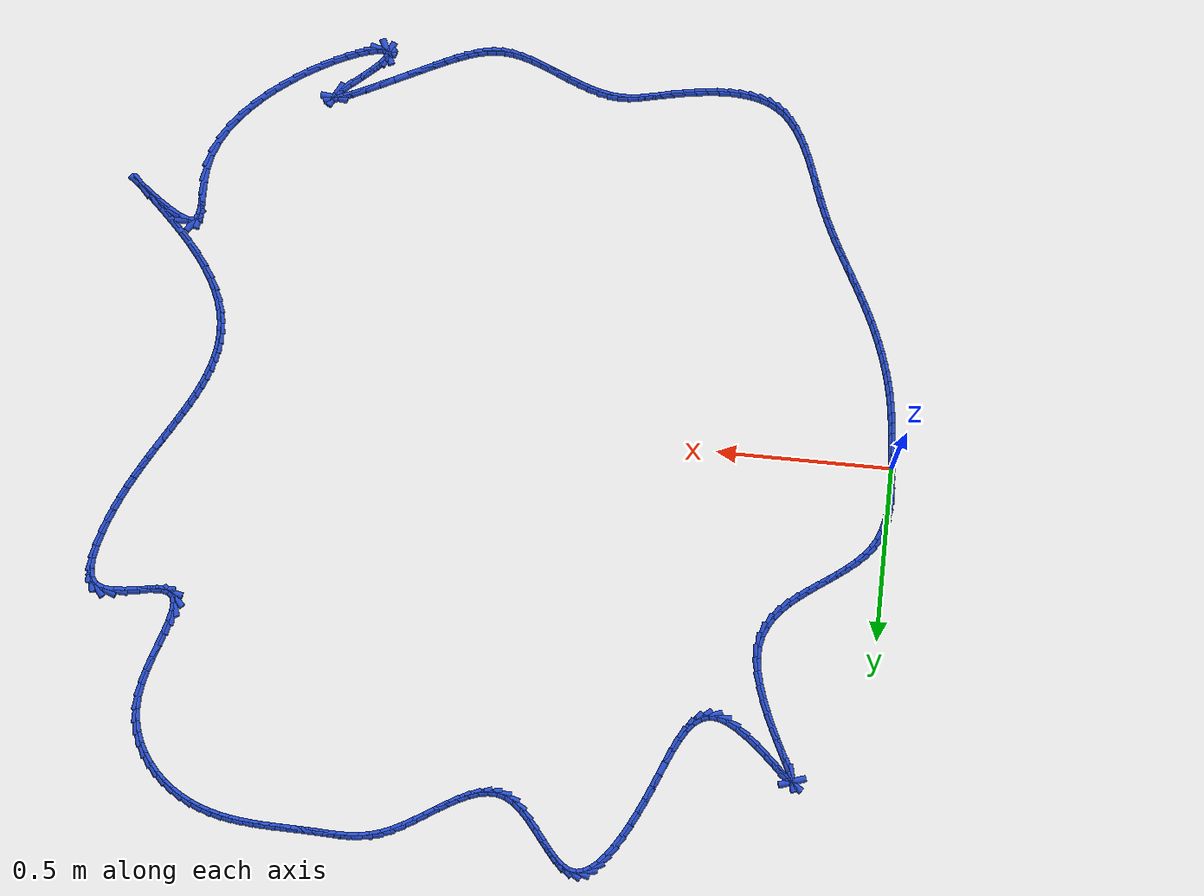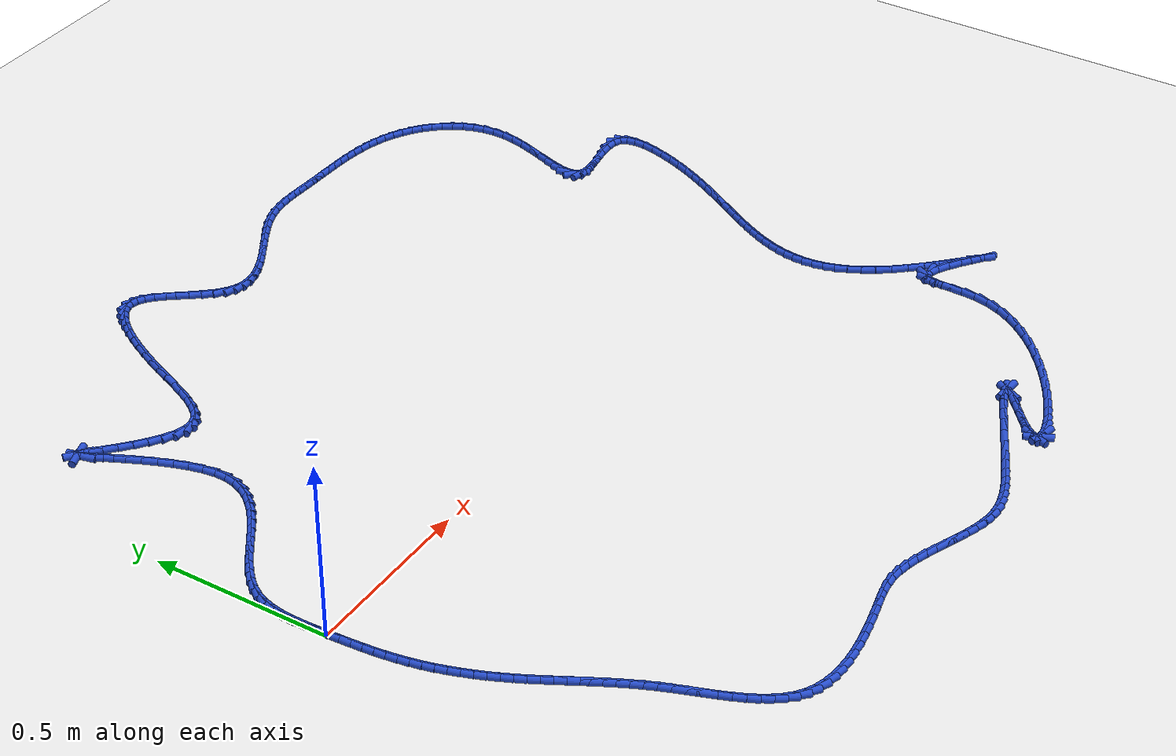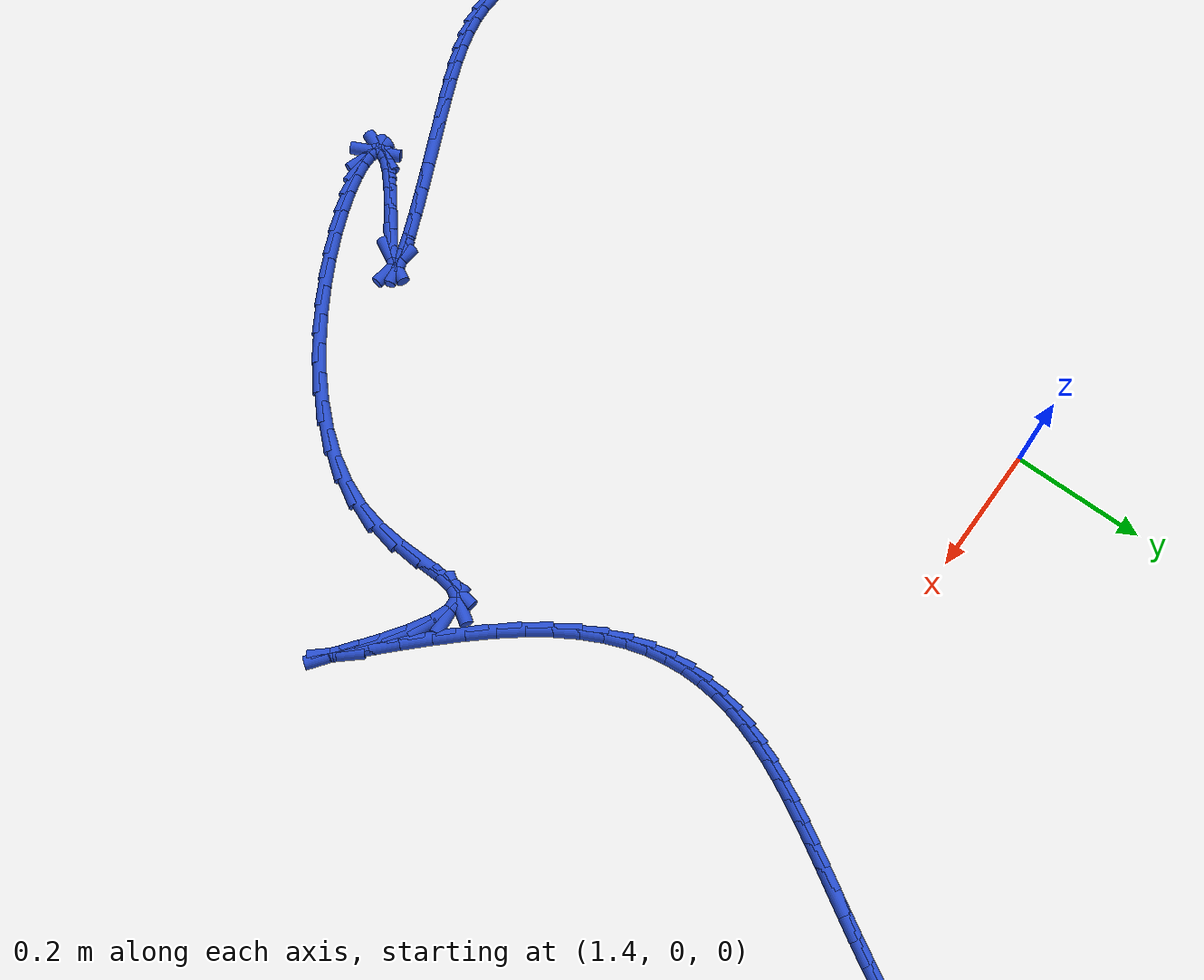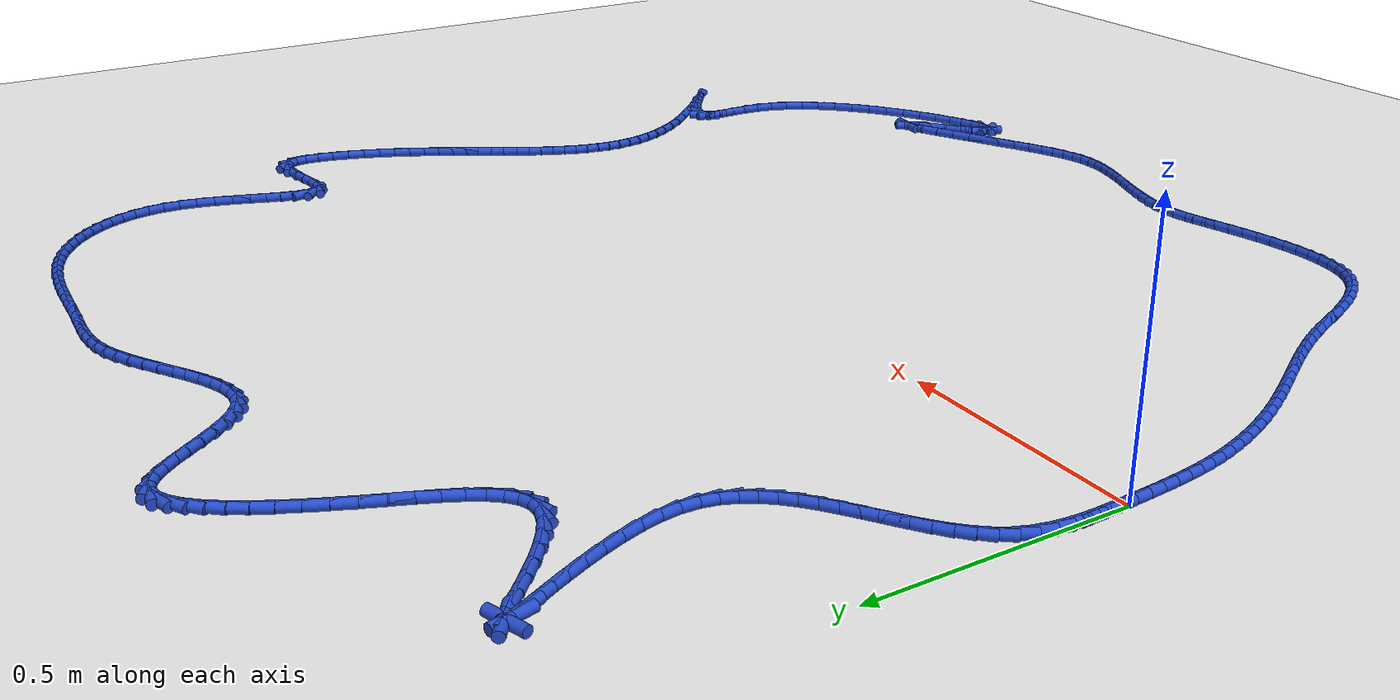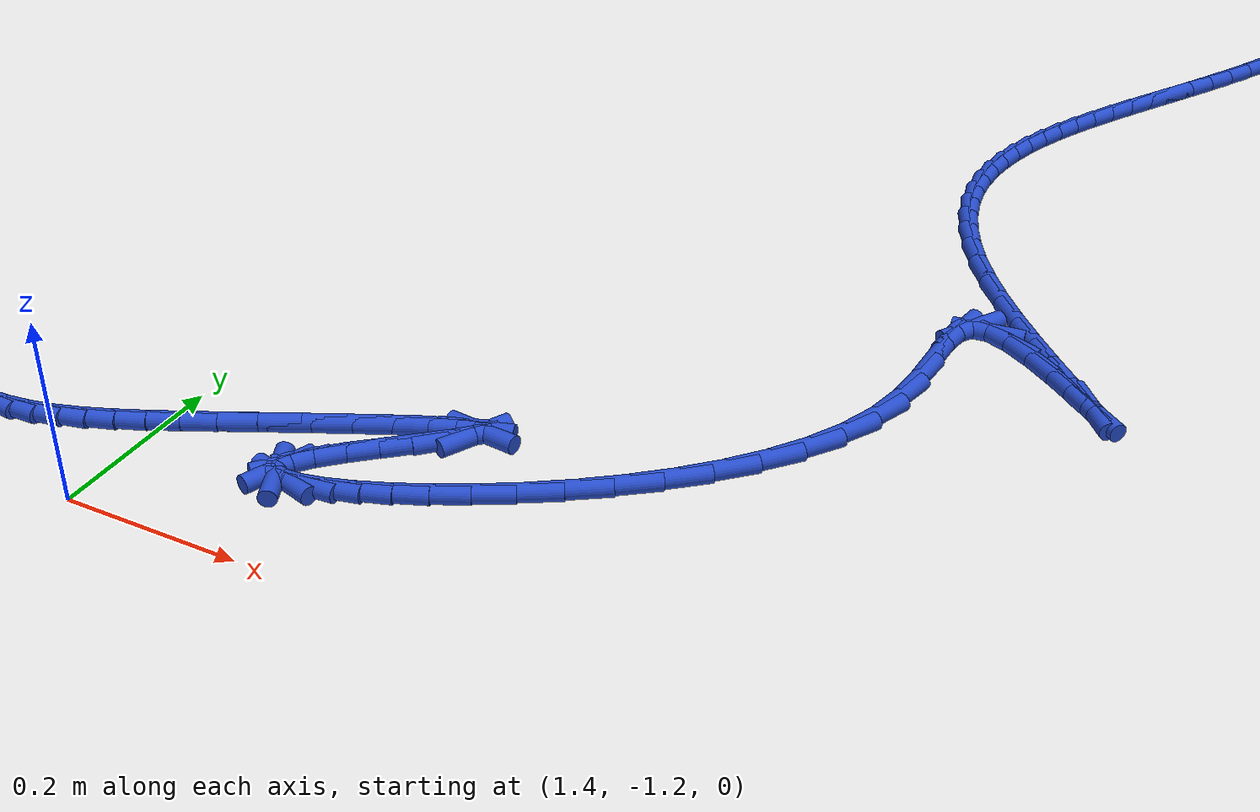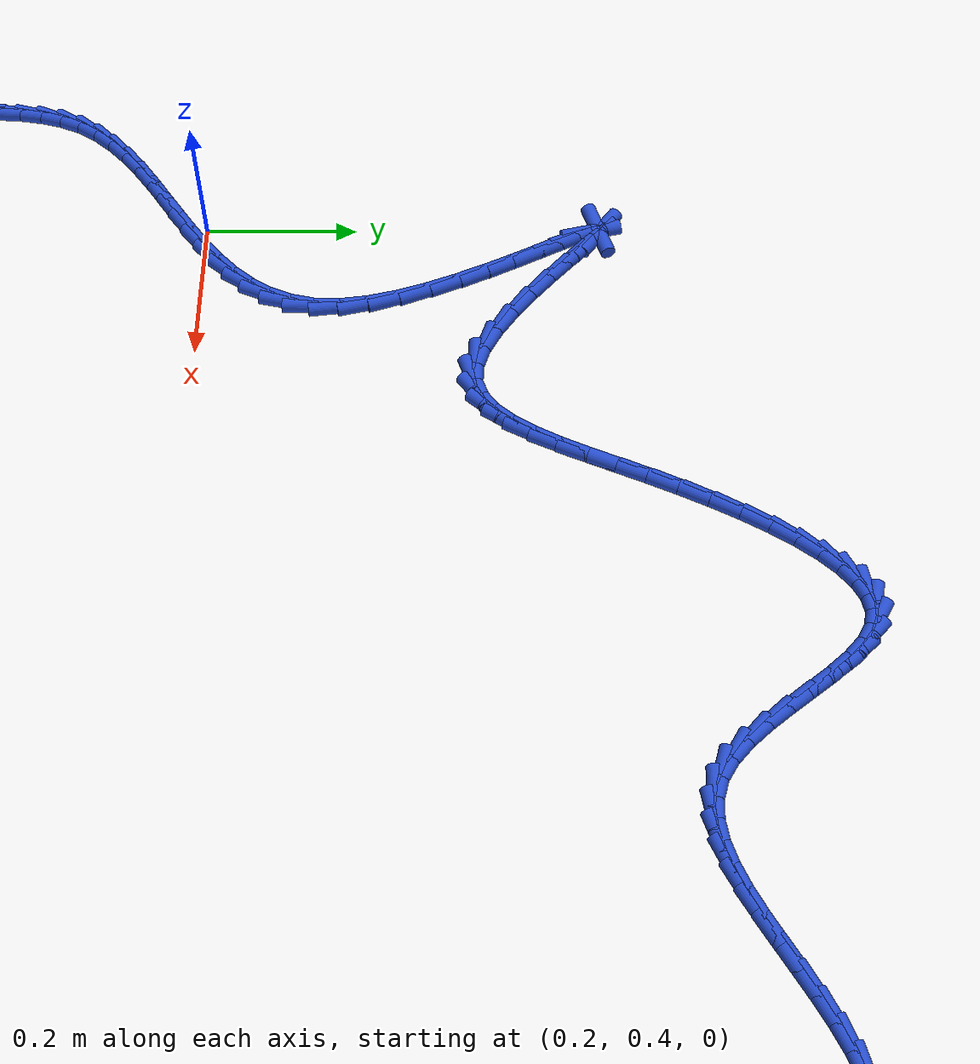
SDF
<sdf version="1.6">
 <world name="default">
  <light name="sun" type="directional">
   <pose>0 0 10 0 -0 0</pose>
   <diffuse>0.8 0.8 0.8 1</diffuse>
   <specular>0.2 0.2 0.2 1</specular>
   <attenuation>
    <range>1000</range>
    <constant>0.9</constant>
    <linear>0.01</linear>
    <quadratic>0.001</quadratic>
   </attenuation>
   <direction>-0.5 0.1 -0.9</direction>
  </light>
  <model name="ground_plane">
   <static>1</static>
   <link name="link">
    <collision name="collision">
     <geometry><plane><normal>0 0 1</normal><size>100 100</size></plane></geometry>
     <surface><friction><ode><mu>100</mu><mu2>50</mu2></ode></friction></surface>
    </collision>
    <visual name="visual">
     <cast_shadows>0</cast_shadows>
     <geometry><plane><normal>0 0 1</normal><size>100 100</size></plane></geometry>
     <material>
      <script><uri>file://media/materials/scripts/gazebo.material</uri><name>Gazebo/WhiteGlow</name></script>
     </material>
    </visual>
   </link>
  </model>
  <gravity>0 0 -9.8</gravity>
  <magnetic_field>6e-06 2.3e-05 -4.2e-05</magnetic_field>
  <atmosphere type="adiabatic"/>
  <physics name="default_physics" default="0" type="ode">
   <max_step_size>0.001</max_step_size>
   <real_time_factor>1</real_time_factor>
   <real_time_update_rate>1000</real_time_update_rate>
  </physics>
  <scene><ambient>0.4 0.4 0.4 1</ambient><background>0.7 0.7 0.7 1</background><shadows>1</shadows></scene>
  <spherical_coordinates>
   <surface_model>EARTH_WGS84</surface_model>
   <latitude_deg>0</latitude_deg>
   <longitude_deg>0</longitude_deg>
   <elevation>0</elevation>
   <heading_deg>0</heading_deg>
  </spherical_coordinates>
  <model name="line">
   <link name="link_0">
    <pose>1.6479873021779667e-17 -1.3877787807814457e-17 0.01 0 1.57 -1.5169289037299356</pose>
    <collision name="collision">
     <geometry><cylinder><radius>0.01</radius><length>0.08</length></cylinder></geometry>
    </collision>
    <visual name="visual">
     <material>
      <script><name>Gazebo/Blue</name><uri>file://media/materials/scripts/gazebo.material</uri></script>
     </material>
     <geometry><cylinder><radius>0.01</radius><length>0.08</length></cylinder></geometry>
    </visual>
   </link>
   <link name="link_1">
    <pose>-0.0017081246326185085 0.03167911255385943 0.01 0 1.57 -1.5366417405871349</pose>
    <collision name="collision">
     <geometry><cylinder><radius>0.01</radius><length>0.08</length></cylinder></geometry>
    </collision>
    <visual name="visual">
     <material>
      <script><name>Gazebo/Blue</name><uri>file://media/materials/scripts/gazebo.material</uri></script>
     </material>
     <geometry><cylinder><radius>0.01</radius><length>0.08</length></cylinder></geometry>
    </visual>
   </link>
   <link name="link_2">
    <pose>-0.0027959164126874657 0.06351579644415624 0.01 0 1.57 1.5668645503999694</pose>
    <collision name="collision">
     <geometry><cylinder><radius>0.01</radius><length>0.08</length></cylinder></geometry>
    </collision>
    <visual name="visual">
     <material>
      <script><name>Gazebo/Blue</name><uri>file://media/materials/scripts/gazebo.material</uri></script>
     </material>
     <geometry><cylinder><radius>0.01</radius><length>0.08</length></cylinder></geometry>
    </visual>
   </link>
   <link name="link_3">
    <pose>-0.0026716082320646997 0.09513192299397714 0.01 0 1.57 1.5087119891368779</pose>
    <collision name="collision">
     <geometry><cylinder><radius>0.01</radius><length>0.08</length></cylinder></geometry>
    </collision>
    <visual name="visual">
     <material>
      <script><name>Gazebo/Blue</name><uri>file://media/materials/scripts/gazebo.material</uri></script>
     </material>
     <geometry><cylinder><radius>0.01</radius><length>0.08</length></cylinder></geometry>
    </visual>
   </link>
   <link name="link_4">
    <pose>-0.0007434329826080588 0.12614936352640913 0.01 0 1.57 1.4278460036132272</pose>
    <collision name="collision">
     <geometry><cylinder><radius>0.01</radius><length>0.08</length></cylinder></geometry>
    </collision>
    <visual name="visual">
     <material>
      <script><name>Gazebo/Blue</name><uri>file://media/materials/scripts/gazebo.material</uri></script>
     </material>
     <geometry><cylinder><radius>0.01</radius><length>0.08</length></cylinder></geometry>
    </visual>
   </link>
   <link name="link_5">
    <pose>0.003580376443824612 0.1561899893645388 0.01 0 1.57 1.3212364394583436</pose>
    <collision name="collision">
     <geometry><cylinder><radius>0.01</radius><length>0.08</length></cylinder></geometry>
    </collision>
    <visual name="visual">
     <material>
      <script><name>Gazebo/Blue</name><uri>file://media/materials/scripts/gazebo.material</uri></script>
     </material>
     <geometry><cylinder><radius>0.01</radius><length>0.08</length></cylinder></geometry>
    </visual>
   </link>
   <link name="link_6">
    <pose>0.010891587155375467 0.18487567183145304 0.01 0 1.57 1.1867978124770695</pose>
    <collision name="collision">
     <geometry><cylinder><radius>0.01</radius><length>0.08</length></cylinder></geometry>
    </collision>
    <visual name="visual">
     <material>
      <script><name>Gazebo/Blue</name><uri>file://media/materials/scripts/gazebo.material</uri></script>
     </material>
     <geometry><cylinder><radius>0.01</radius><length>0.08</length></cylinder></geometry>
    </visual>
   </link>
   <link name="link_7">
    <pose>0.021781966260186664 0.21182828225023886 0.01 0 1.57 1.031378172145254</pose>
    <collision name="collision">
     <geometry><cylinder><radius>0.01</radius><length>0.08</length></cylinder></geometry>
    </collision>
    <visual name="visual">
     <material>
      <script><name>Gazebo/Blue</name><uri>file://media/materials/scripts/gazebo.material</uri></script>
     </material>
     <geometry><cylinder><radius>0.01</radius><length>0.08</length></cylinder></geometry>
    </visual>
   </link>
   <link name="link_8">
    <pose>0.03670214508740581 0.23675178229962057 0.01 0 1.57 0.8927171543347373</pose>
    <collision name="collision">
     <geometry><cylinder><radius>0.01</radius><length>0.08</length></cylinder></geometry>
    </collision>
    <visual name="visual">
     <material>
      <script><name>Gazebo/Blue</name><uri>file://media/materials/scripts/gazebo.material</uri></script>
     </material>
     <geometry><cylinder><radius>0.01</radius><length>0.08</length></cylinder></geometry>
    </visual>
   </link>
   <link name="link_9">
    <pose>0.055287042813328746 0.25982458529066454 0.01 0 1.57 0.784898827575356</pose>
    <collision name="collision">
     <geometry><cylinder><radius>0.01</radius><length>0.08</length></cylinder></geometry>
    </collision>
    <visual name="visual">
     <material>
      <script><name>Gazebo/Blue</name><uri>file://media/materials/scripts/gazebo.material</uri></script>
     </material>
     <geometry><cylinder><radius>0.01</radius><length>0.08</length></cylinder></geometry>
    </visual>
   </link>
   <link name="link_10">
    <pose>0.07687918365320512 0.28139517343199005 0.01 0 1.57 0.7061109310032161</pose>
    <collision name="collision">
     <geometry><cylinder><radius>0.01</radius><length>0.08</length></cylinder></geometry>
    </collision>
    <visual name="visual">
     <material>
      <script><name>Gazebo/Blue</name><uri>file://media/materials/scripts/gazebo.material</uri></script>
     </material>
     <geometry><cylinder><radius>0.01</radius><length>0.08</length></cylinder></geometry>
    </visual>
   </link>
   <link name="link_11">
    <pose>0.10082071693396542 0.301812246982634 0.01 0 1.57 0.6531049567065565</pose>
    <collision name="collision">
     <geometry><cylinder><radius>0.01</radius><length>0.08</length></cylinder></geometry>
    </collision>
    <visual name="visual">
     <material>
      <script><name>Gazebo/Blue</name><uri>file://media/materials/scripts/gazebo.material</uri></script>
     </material>
     <geometry><cylinder><radius>0.01</radius><length>0.08</length></cylinder></geometry>
    </visual>
   </link>
   <link name="link_12">
    <pose>0.1264537919825401 0.3214245062016331 0.01 0 1.57 0.6229373550466749</pose>
    <collision name="collision">
     <geometry><cylinder><radius>0.01</radius><length>0.08</length></cylinder></geometry>
    </collision>
    <visual name="visual">
     <material>
      <script><name>Gazebo/Blue</name><uri>file://media/materials/scripts/gazebo.material</uri></script>
     </material>
     <geometry><cylinder><radius>0.01</radius><length>0.08</length></cylinder></geometry>
    </visual>
   </link>
   <link name="link_13">
    <pose>0.1531205581258596 0.34058065134802373 0.01 0 1.57 0.613670889038933</pose>
    <collision name="collision">
     <geometry><cylinder><radius>0.01</radius><length>0.08</length></cylinder></geometry>
    </collision>
    <visual name="visual">
     <material>
      <script><name>Gazebo/Blue</name><uri>file://media/materials/scripts/gazebo.material</uri></script>
     </material>
     <geometry><cylinder><radius>0.01</radius><length>0.08</length></cylinder></geometry>
    </visual>
   </link>
   <link name="link_14">
    <pose>0.1801631646908543 0.35962938268084266 0.01 0 1.57 0.6245738218739101</pose>
    <collision name="collision">
     <geometry><cylinder><radius>0.01</radius><length>0.08</length></cylinder></geometry>
    </collision>
    <visual name="visual">
     <material>
      <script><name>Gazebo/Blue</name><uri>file://media/materials/scripts/gazebo.material</uri></script>
     </material>
     <geometry><cylinder><radius>0.01</radius><length>0.08</length></cylinder></geometry>
    </visual>
   </link>
   <link name="link_15">
    <pose>0.20692376100445467 0.37891940045912637 0.01 0 1.57 0.6561310193265922</pose>
    <collision name="collision">
     <geometry><cylinder><radius>0.01</radius><length>0.08</length></cylinder></geometry>
    </collision>
    <visual name="visual">
     <material>
      <script><name>Gazebo/Blue</name><uri>file://media/materials/scripts/gazebo.material</uri></script>
     </material>
     <geometry><cylinder><radius>0.01</radius><length>0.08</length></cylinder></geometry>
    </visual>
   </link>
   <link name="link_16">
    <pose>0.23274449639359127 0.3987994049419118 0.01 0 1.57 0.7099598297764018</pose>
    <collision name="collision">
     <geometry><cylinder><radius>0.01</radius><length>0.08</length></cylinder></geometry>
    </collision>
    <visual name="visual">
     <material>
      <script><name>Gazebo/Blue</name><uri>file://media/materials/scripts/gazebo.material</uri></script>
     </material>
     <geometry><cylinder><radius>0.01</radius><length>0.08</length></cylinder></geometry>
    </visual>
   </link>
   <link name="link_17">
    <pose>0.25696752018519436 0.4196180963882353 0.01 0 1.57 0.788543286077477</pose>
    <collision name="collision">
     <geometry><cylinder><radius>0.01</radius><length>0.08</length></cylinder></geometry>
    </collision>
    <visual name="visual">
     <material>
      <script><name>Gazebo/Blue</name><uri>file://media/materials/scripts/gazebo.material</uri></script>
     </material>
     <geometry><cylinder><radius>0.01</radius><length>0.08</length></cylinder></geometry>
    </visual>
   </link>
   <link name="link_18">
    <pose>0.27893498170619446 0.44172417505713363 0.01 0 1.57 0.8945082515153614</pose>
    <collision name="collision">
     <geometry><cylinder><radius>0.01</radius><length>0.08</length></cylinder></geometry>
    </collision>
    <visual name="visual">
     <material>
      <script><name>Gazebo/Blue</name><uri>file://media/materials/scripts/gazebo.material</uri></script>
     </material>
     <geometry><cylinder><radius>0.01</radius><length>0.08</length></cylinder></geometry>
    </visual>
   </link>
   <link name="link_19">
    <pose>0.297989030283522 0.46546634120764335 0.01 0 1.57 1.029045670293951</pose>
    <collision name="collision">
     <geometry><cylinder><radius>0.01</radius><length>0.08</length></cylinder></geometry>
    </collision>
    <visual name="visual">
     <material>
      <script><name>Gazebo/Blue</name><uri>file://media/materials/scripts/gazebo.material</uri></script>
     </material>
     <geometry><cylinder><radius>0.01</radius><length>0.08</length></cylinder></geometry>
    </visual>
   </link>
   <link name="link_20">
    <pose>0.3134718152441075 0.49119329509880116 0.01 0 1.57 1.189384170315574</pose>
    <collision name="collision">
     <geometry><cylinder><radius>0.01</radius><length>0.08</length></cylinder></geometry>
    </collision>
    <visual name="visual">
     <material>
      <script><name>Gazebo/Blue</name><uri>file://media/materials/scripts/gazebo.material</uri></script>
     </material>
     <geometry><cylinder><radius>0.01</radius><length>0.08</length></cylinder></geometry>
    </visual>
   </link>
   <link name="link_21">
    <pose>0.3247254859148814 0.5192537369896437 0.01 0 1.57 1.3665861587407233</pose>
    <collision name="collision">
     <geometry><cylinder><radius>0.01</radius><length>0.08</length></cylinder></geometry>
    </collision>
    <visual name="visual">
     <material>
      <script><name>Gazebo/Blue</name><uri>file://media/materials/scripts/gazebo.material</uri></script>
     </material>
     <geometry><cylinder><radius>0.01</radius><length>0.08</length></cylinder></geometry>
    </visual>
   </link>
   <link name="link_22">
    <pose>0.3310921916227739 0.5499963671392075 0.01 0 1.57 1.5462722711945407</pose>
    <collision name="collision">
     <geometry><cylinder><radius>0.01</radius><length>0.08</length></cylinder></geometry>
    </collision>
    <visual name="visual">
     <material>
      <script><name>Gazebo/Blue</name><uri>file://media/materials/scripts/gazebo.material</uri></script>
     </material>
     <geometry><cylinder><radius>0.01</radius><length>0.08</length></cylinder></geometry>
    </visual>
   </link>
   <link name="link_23">
    <pose>0.3319204962589454 0.5837647856849958 0.01 0 1.57 -1.4412416503928223</pose>
    <collision name="collision">
     <geometry><cylinder><radius>0.01</radius><length>0.08</length></cylinder></geometry>
    </collision>
    <visual name="visual">
     <material>
      <script><name>Gazebo/Blue</name><uri>file://media/materials/scripts/gazebo.material</uri></script>
     </material>
     <geometry><cylinder><radius>0.01</radius><length>0.08</length></cylinder></geometry>
    </visual>
   </link>
   <link name="link_24">
    <pose>0.3271424619114956 0.6204386623068459 0.01 0 1.57 -1.3318536267235894</pose>
    <collision name="collision">
     <geometry><cylinder><radius>0.01</radius><length>0.08</length></cylinder></geometry>
    </collision>
    <visual name="visual">
     <material>
      <script><name>Gazebo/Blue</name><uri>file://media/materials/scripts/gazebo.material</uri></script>
     </material>
     <geometry><cylinder><radius>0.01</radius><length>0.08</length></cylinder></geometry>
    </visual>
   </link>
   <link name="link_25">
    <pose>0.31773221903037974 0.6590691341294445 0.01 0 1.57 -1.2541452055621358</pose>
    <collision name="collision">
     <geometry><cylinder><radius>0.01</radius><length>0.08</length></cylinder></geometry>
    </collision>
    <visual name="visual">
     <material>
      <script><name>Gazebo/Blue</name><uri>file://media/materials/scripts/gazebo.material</uri></script>
     </material>
     <geometry><cylinder><radius>0.01</radius><length>0.08</length></cylinder></geometry>
    </visual>
   </link>
   <link name="link_26">
    <pose>0.30477181142227305 0.6986215380243946 0.01 0 1.57 -1.1979050699701133</pose>
    <collision name="collision">
     <geometry><cylinder><radius>0.01</radius><length>0.08</length></cylinder></geometry>
    </collision>
    <visual name="visual">
     <material>
      <script><name>Gazebo/Blue</name><uri>file://media/materials/scripts/gazebo.material</uri></script>
     </material>
     <geometry><cylinder><radius>0.01</radius><length>0.08</length></cylinder></geometry>
    </visual>
   </link>
   <link name="link_27">
    <pose>0.28934328289385025 0.7380612108633 0.01 0 1.57 -1.1570335195105463</pose>
    <collision name="collision">
     <geometry><cylinder><radius>0.01</radius><length>0.08</length></cylinder></geometry>
    </collision>
    <visual name="visual">
     <material>
      <script><name>Gazebo/Blue</name><uri>file://media/materials/scripts/gazebo.material</uri></script>
     </material>
     <geometry><cylinder><radius>0.01</radius><length>0.08</length></cylinder></geometry>
    </visual>
   </link>
   <link name="link_28">
    <pose>0.27252867725178637 0.776353489517764 0.01 0 1.57 -1.1281100830862631</pose>
    <collision name="collision">
     <geometry><cylinder><radius>0.01</radius><length>0.08</length></cylinder></geometry>
    </collision>
    <visual name="visual">
     <material>
      <script><name>Gazebo/Blue</name><uri>file://media/materials/scripts/gazebo.material</uri></script>
     </material>
     <geometry><cylinder><radius>0.01</radius><length>0.08</length></cylinder></geometry>
    </visual>
   </link>
   <link name="link_29">
    <pose>0.25541003830275666 0.8124637108593896 0.01 0 1.57 -1.1097330311195828</pose>
    <collision name="collision">
     <geometry><cylinder><radius>0.01</radius><length>0.08</length></cylinder></geometry>
    </collision>
    <visual name="visual">
     <material>
      <script><name>Gazebo/Blue</name><uri>file://media/materials/scripts/gazebo.material</uri></script>
     </material>
     <geometry><cylinder><radius>0.01</radius><length>0.08</length></cylinder></geometry>
    </visual>
   </link>
   <link name="link_30">
    <pose>0.2390694098534361 0.8453572117597803 0.01 0 1.57 -1.102703240145169</pose>
    <collision name="collision">
     <geometry><cylinder><radius>0.01</radius><length>0.08</length></cylinder></geometry>
    </collision>
    <visual name="visual">
     <material>
      <script><name>Gazebo/Blue</name><uri>file://media/materials/scripts/gazebo.material</uri></script>
     </material>
     <geometry><cylinder><radius>0.01</radius><length>0.08</length></cylinder></geometry>
    </visual>
   </link>
   <link name="link_31">
    <pose>0.2245888357104996 0.8739993290905391 0.01 0 1.57 -1.1119403655011126</pose>
    <collision name="collision">
     <geometry><cylinder><radius>0.01</radius><length>0.08</length></cylinder></geometry>
    </collision>
    <visual name="visual">
     <material>
      <script><name>Gazebo/Blue</name><uri>file://media/materials/scripts/gazebo.material</uri></script>
     </material>
     <geometry><cylinder><radius>0.01</radius><length>0.08</length></cylinder></geometry>
    </visual>
   </link>
   <link name="link_32">
    <pose>0.2130503596806222 0.89735539972327 0.01 0 1.57 -1.1553664526700589</pose>
    <collision name="collision">
     <geometry><cylinder><radius>0.01</radius><length>0.08</length></cylinder></geometry>
    </collision>
    <visual name="visual">
     <material>
      <script><name>Gazebo/Blue</name><uri>file://media/materials/scripts/gazebo.material</uri></script>
     </material>
     <geometry><cylinder><radius>0.01</radius><length>0.08</length></cylinder></geometry>
    </visual>
   </link>
   <link name="link_33">
    <pose>0.2055360255704789 0.914390760529576 0.01 0 1.57 -1.3269700216863092</pose>
    <collision name="collision">
     <geometry><cylinder><radius>0.01</radius><length>0.08</length></cylinder></geometry>
    </collision>
    <visual name="visual">
     <material>
      <script><name>Gazebo/Blue</name><uri>file://media/materials/scripts/gazebo.material</uri></script>
     </material>
     <geometry><cylinder><radius>0.01</radius><length>0.08</length></cylinder></geometry>
    </visual>
   </link>
   <link name="link_34">
    <pose>0.20312787718674483 0.9240707483810602 0.01 0 1.57 0.32885833397499126</pose>
    <collision name="collision">
     <geometry><cylinder><radius>0.01</radius><length>0.08</length></cylinder></geometry>
    </collision>
    <visual name="visual">
     <material>
      <script><name>Gazebo/Blue</name><uri>file://media/materials/scripts/gazebo.material</uri></script>
     </material>
     <geometry><cylinder><radius>0.01</radius><length>0.08</length></cylinder></geometry>
    </visual>
   </link>
   <link name="link_35">
    <pose>0.20690795833609488 0.9253607001493258 0.01 0 1.57 -0.6199399838525371</pose>
    <collision name="collision">
     <geometry><cylinder><radius>0.01</radius><length>0.08</length></cylinder></geometry>
    </collision>
    <visual name="visual">
     <material>
      <script><name>Gazebo/Blue</name><uri>file://media/materials/scripts/gazebo.material</uri></script>
     </material>
     <geometry><cylinder><radius>0.01</radius><length>0.08</length></cylinder></geometry>
    </visual>
   </link>
   <link name="link_36">
    <pose>0.21759446600557827 0.917732474276856 0.01 0 1.57 -0.7283895927231969</pose>
    <collision name="collision">
     <geometry><cylinder><radius>0.01</radius><length>0.08</length></cylinder></geometry>
    </collision>
    <visual name="visual">
     <material>
      <script><name>Gazebo/Blue</name><uri>file://media/materials/scripts/gazebo.material</uri></script>
     </material>
     <geometry><cylinder><radius>0.01</radius><length>0.08</length></cylinder></geometry>
    </visual>
   </link>
   <link name="link_37">
    <pose>0.23442467154054775 0.9027195681759547 0.01 0 1.57 -0.7499691526827266</pose>
    <collision name="collision">
     <geometry><cylinder><radius>0.01</radius><length>0.08</length></cylinder></geometry>
    </collision>
    <visual name="visual">
     <material>
      <script><name>Gazebo/Blue</name><uri>file://media/materials/scripts/gazebo.material</uri></script>
     </material>
     <geometry><cylinder><radius>0.01</radius><length>0.08</length></cylinder></geometry>
    </visual>
   </link>
   <link name="link_38">
    <pose>0.25625911865028056 0.8823799325830343 0.01 0 1.57 -0.7430200246903909</pose>
    <collision name="collision">
     <geometry><cylinder><radius>0.01</radius><length>0.08</length></cylinder></geometry>
    </collision>
    <visual name="visual">
     <material>
      <script><name>Gazebo/Blue</name><uri>file://media/materials/scripts/gazebo.material</uri></script>
     </material>
     <geometry><cylinder><radius>0.01</radius><length>0.08</length></cylinder></geometry>
    </visual>
   </link>
   <link name="link_39">
    <pose>0.2819583509718768 0.8587715183349862 0.01 0 1.57 -0.7177879676649651</pose>
    <collision name="collision">
     <geometry><cylinder><radius>0.01</radius><length>0.08</length></cylinder></geometry>
    </collision>
    <visual name="visual">
     <material>
      <script><name>Gazebo/Blue</name><uri>file://media/materials/scripts/gazebo.material</uri></script>
     </material>
     <geometry><cylinder><radius>0.01</radius><length>0.08</length></cylinder></geometry>
    </visual>
   </link>
   <link name="link_40">
    <pose>0.31038291214243646 0.8339522762687029 0.01 0 1.57 -0.6740044256709823</pose>
    <collision name="collision">
     <geometry><cylinder><radius>0.01</radius><length>0.08</length></cylinder></geometry>
    </collision>
    <visual name="visual">
     <material>
      <script><name>Gazebo/Blue</name><uri>file://media/materials/scripts/gazebo.material</uri></script>
     </material>
     <geometry><cylinder><radius>0.01</radius><length>0.08</length></cylinder></geometry>
    </visual>
   </link>
   <link name="link_41">
    <pose>0.3403933457990593 0.8099801572210763 0.01 0 1.57 -0.6051346839254056</pose>
    <collision name="collision">
     <geometry><cylinder><radius>0.01</radius><length>0.08</length></cylinder></geometry>
    </collision>
    <visual name="visual">
     <material>
      <script><name>Gazebo/Blue</name><uri>file://media/materials/scripts/gazebo.material</uri></script>
     </material>
     <geometry><cylinder><radius>0.01</radius><length>0.08</length></cylinder></geometry>
    </visual>
   </link>
   <link name="link_42">
    <pose>0.3708501955788452 0.7889131120289982 0.01 0 1.57 -0.49595394357340283</pose>
    <collision name="collision">
     <geometry><cylinder><radius>0.01</radius><length>0.08</length></cylinder></geometry>
    </collision>
    <visual name="visual">
     <material>
      <script><name>Gazebo/Blue</name><uri>file://media/materials/scripts/gazebo.material</uri></script>
     </material>
     <geometry><cylinder><radius>0.01</radius><length>0.08</length></cylinder></geometry>
    </visual>
   </link>
   <link name="link_43">
    <pose>0.40061400511889383 0.7728090915293606 0.01 0 1.57 -0.3144057232918719</pose>
    <collision name="collision">
     <geometry><cylinder><radius>0.01</radius><length>0.08</length></cylinder></geometry>
    </collision>
    <visual name="visual">
     <material>
      <script><name>Gazebo/Blue</name><uri>file://media/materials/scripts/gazebo.material</uri></script>
     </material>
     <geometry><cylinder><radius>0.01</radius><length>0.08</length></cylinder></geometry>
    </visual>
   </link>
   <link name="link_44">
    <pose>0.4285453180563058 0.7637260465590554 0.01 0 1.57 -0.011703591210170897</pose>
    <collision name="collision">
     <geometry><cylinder><radius>0.01</radius><length>0.08</length></cylinder></geometry>
    </collision>
    <visual name="visual">
     <material>
      <script><name>Gazebo/Blue</name><uri>file://media/materials/scripts/gazebo.material</uri></script>
     </material>
     <geometry><cylinder><radius>0.01</radius><length>0.08</length></cylinder></geometry>
    </visual>
   </link>
   <link name="link_45">
    <pose>0.45365351735670106 0.7634321770407985 0.01 0 1.57 0.35485432812626344</pose>
    <collision name="collision">
     <geometry><cylinder><radius>0.01</radius><length>0.08</length></cylinder></geometry>
    </collision>
    <visual name="visual">
     <material>
      <script><name>Gazebo/Blue</name><uri>file://media/materials/scripts/gazebo.material</uri></script>
     </material>
     <geometry><cylinder><radius>0.01</radius><length>0.08</length></cylinder></geometry>
    </visual>
   </link>
   <link name="link_46">
    <pose>0.4759720614419376 0.7717020780982234 0.01 0 1.57 0.6678376235612845</pose>
    <collision name="collision">
     <geometry><cylinder><radius>0.01</radius><length>0.08</length></cylinder></geometry>
    </collision>
    <visual name="visual">
     <material>
      <script><name>Gazebo/Blue</name><uri>file://media/materials/scripts/gazebo.material</uri></script>
     </material>
     <geometry><cylinder><radius>0.01</radius><length>0.08</length></cylinder></geometry>
    </visual>
   </link>
   <link name="link_47">
    <pose>0.4959652842543108 0.7874715438661151 0.01 0 1.57 0.8859163377391943</pose>
    <collision name="collision">
     <geometry><cylinder><radius>0.01</radius><length>0.08</length></cylinder></geometry>
    </collision>
    <visual name="visual">
     <material>
      <script><name>Gazebo/Blue</name><uri>file://media/materials/scripts/gazebo.material</uri></script>
     </material>
     <geometry><cylinder><radius>0.01</radius><length>0.08</length></cylinder></geometry>
    </visual>
   </link>
   <link name="link_48">
    <pose>0.5140990174254307 0.8096734528731955 0.01 0 1.57 1.025066322846191</pose>
    <collision name="collision">
     <geometry><cylinder><radius>0.01</radius><length>0.08</length></cylinder></geometry>
    </collision>
    <visual name="visual">
     <material>
      <script><name>Gazebo/Blue</name><uri>file://media/materials/scripts/gazebo.material</uri></script>
     </material>
     <geometry><cylinder><radius>0.01</radius><length>0.08</length></cylinder></geometry>
    </visual>
   </link>
   <link name="link_49">
    <pose>0.530839092586908 0.8372406836481885 0.01 0 1.57 1.1101776761175524</pose>
    <collision name="collision">
     <geometry><cylinder><radius>0.01</radius><length>0.08</length></cylinder></geometry>
    </collision>
    <visual name="visual">
     <material>
      <script><name>Gazebo/Blue</name><uri>file://media/materials/scripts/gazebo.material</uri></script>
     </material>
     <geometry><cylinder><radius>0.01</radius><length>0.08</length></cylinder></geometry>
    </visual>
   </link>
   <link name="link_50">
    <pose>0.5466513413703532 0.8691061147198168 0.01 0 1.57 1.1584927687857978</pose>
    <collision name="collision">
     <geometry><cylinder><radius>0.01</radius><length>0.08</length></cylinder></geometry>
    </collision>
    <visual name="visual">
     <material>
      <script><name>Gazebo/Blue</name><uri>file://media/materials/scripts/gazebo.material</uri></script>
     </material>
     <geometry><cylinder><radius>0.01</radius><length>0.08</length></cylinder></geometry>
    </visual>
   </link>
   <link name="link_51">
    <pose>0.5620015954073766 0.9042026246168028 0.01 0 1.57 1.1799243712703809</pose>
    <collision name="collision">
     <geometry><cylinder><radius>0.01</radius><length>0.08</length></cylinder></geometry>
    </collision>
    <visual name="visual">
     <material>
      <script><name>Gazebo/Blue</name><uri>file://media/materials/scripts/gazebo.material</uri></script>
     </material>
     <geometry><cylinder><radius>0.01</radius><length>0.08</length></cylinder></geometry>
    </visual>
   </link>
   <link name="link_52">
    <pose>0.5773556863295888 0.9414630918678701 0.01 0 1.57 1.179538955681841</pose>
    <collision name="collision">
     <geometry><cylinder><radius>0.01</radius><length>0.08</length></cylinder></geometry>
    </collision>
    <visual name="visual">
     <material>
      <script><name>Gazebo/Blue</name><uri>file://media/materials/scripts/gazebo.material</uri></script>
     </material>
     <geometry><cylinder><radius>0.01</radius><length>0.08</length></cylinder></geometry>
    </visual>
   </link>
   <link name="link_53">
    <pose>0.5931791229010174 0.9798205668883077 0.01 0 1.57 1.1629228723960348</pose>
    <collision name="collision">
     <geometry><cylinder><radius>0.01</radius><length>0.08</length></cylinder></geometry>
    </collision>
    <visual name="visual">
     <material>
      <script><name>Gazebo/Blue</name><uri>file://media/materials/scripts/gazebo.material</uri></script>
     </material>
     <geometry><cylinder><radius>0.01</radius><length>0.08</length></cylinder></geometry>
    </visual>
   </link>
   <link name="link_54">
    <pose>0.6097985280993995 1.0182820393864562 0.01 0 1.57 1.1392877880767849</pose>
    <collision name="collision">
     <geometry><cylinder><radius>0.01</radius><length>0.08</length></cylinder></geometry>
    </collision>
    <visual name="visual">
     <material>
      <script><name>Gazebo/Blue</name><uri>file://media/materials/scripts/gazebo.material</uri></script>
     </material>
     <geometry><cylinder><radius>0.01</radius><length>0.08</length></cylinder></geometry>
    </visual>
   </link>
   <link name="link_55">
    <pose>0.6271856801082225 1.0560434094979347 0.01 0 1.57 1.108751322990685</pose>
    <collision name="collision">
     <geometry><cylinder><radius>0.01</radius><length>0.08</length></cylinder></geometry>
    </collision>
    <visual name="visual">
     <material>
      <script><name>Gazebo/Blue</name><uri>file://media/materials/scripts/gazebo.material</uri></script>
     </material>
     <geometry><cylinder><radius>0.01</radius><length>0.08</length></cylinder></geometry>
    </visual>
   </link>
   <link name="link_56">
    <pose>0.6452564989403701 1.0923303148409047 0.01 0 1.57 1.0690937379425778</pose>
    <collision name="collision">
     <geometry><cylinder><radius>0.01</radius><length>0.08</length></cylinder></geometry>
    </collision>
    <visual name="visual">
     <material>
      <script><name>Gazebo/Blue</name><uri>file://media/materials/scripts/gazebo.material</uri></script>
     </material>
     <geometry><cylinder><radius>0.01</radius><length>0.08</length></cylinder></geometry>
    </visual>
   </link>
   <link name="link_57">
    <pose>0.6639269046087257 1.126368393033529 0.01 0 1.57 1.016810114287824</pose>
    <collision name="collision">
     <geometry><cylinder><radius>0.01</radius><length>0.08</length></cylinder></geometry>
    </collision>
    <visual name="visual">
     <material>
      <script><name>Gazebo/Blue</name><uri>file://media/materials/scripts/gazebo.material</uri></script>
     </material>
     <geometry><cylinder><radius>0.01</radius><length>0.08</length></cylinder></geometry>
    </visual>
   </link>
   <link name="link_58">
    <pose>0.6831128171261732 1.1573832816939709 0.01 0 1.57 0.9462687745078787</pose>
    <collision name="collision">
     <geometry><cylinder><radius>0.01</radius><length>0.08</length></cylinder></geometry>
    </collision>
    <visual name="visual">
     <material>
      <script><name>Gazebo/Blue</name><uri>file://media/materials/scripts/gazebo.material</uri></script>
     </material>
     <geometry><cylinder><radius>0.01</radius><length>0.08</length></cylinder></geometry>
    </visual>
   </link>
   <link name="link_59">
    <pose>0.7027301565055963 1.184600618440393 0.01 0 1.57 0.8482285060347439</pose>
    <collision name="collision">
     <geometry><cylinder><radius>0.01</radius><length>0.08</length></cylinder></geometry>
    </collision>
    <visual name="visual">
     <material>
      <script><name>Gazebo/Blue</name><uri>file://media/materials/scripts/gazebo.material</uri></script>
     </material>
     <geometry><cylinder><radius>0.01</radius><length>0.08</length></cylinder></geometry>
    </visual>
   </link>
   <link name="link_60">
    <pose>0.7226948427598792 1.2072460408909587 0.01 0 1.57 0.707510914049224</pose>
    <collision name="collision">
     <geometry><cylinder><radius>0.01</radius><length>0.08</length></cylinder></geometry>
    </collision>
    <visual name="visual">
     <material>
      <script><name>Gazebo/Blue</name><uri>file://media/materials/scripts/gazebo.material</uri></script>
     </material>
     <geometry><cylinder><radius>0.01</radius><length>0.08</length></cylinder></geometry>
    </visual>
   </link>
   <link name="link_61">
    <pose>0.7429227959019049 1.22454518666383 0.01 0 1.57 0.5011328090953621</pose>
    <collision name="collision">
     <geometry><cylinder><radius>0.01</radius><length>0.08</length></cylinder></geometry>
    </collision>
    <visual name="visual">
     <material>
      <script><name>Gazebo/Blue</name><uri>file://media/materials/scripts/gazebo.material</uri></script>
     </material>
     <geometry><cylinder><radius>0.01</radius><length>0.08</length></cylinder></geometry>
    </visual>
   </link>
   <link name="link_62">
    <pose>0.7633299359445572 1.2357236933771698 0.01 0 1.57 0.20596580398660785</pose>
    <collision name="collision">
     <geometry><cylinder><radius>0.01</radius><length>0.08</length></cylinder></geometry>
    </collision>
    <visual name="visual">
     <material>
      <script><name>Gazebo/Blue</name><uri>file://media/materials/scripts/gazebo.material</uri></script>
     </material>
     <geometry><cylinder><radius>0.01</radius><length>0.08</length></cylinder></geometry>
    </visual>
   </link>
   <link name="link_63">
    <pose>0.7838321829007202 1.2400071986491408 0.01 0 1.57 -0.16358206487457394</pose>
    <collision name="collision">
     <geometry><cylinder><radius>0.01</radius><length>0.08</length></cylinder></geometry>
    </collision>
    <visual name="visual">
     <material>
      <script><name>Gazebo/Blue</name><uri>file://media/materials/scripts/gazebo.material</uri></script>
     </material>
     <geometry><cylinder><radius>0.01</radius><length>0.08</length></cylinder></geometry>
    </visual>
   </link>
   <link name="link_64">
    <pose>0.8043454567836357 1.2366213401025141 0.01 0 1.57 -0.5079232404879332</pose>
    <collision name="collision">
     <geometry><cylinder><radius>0.01</radius><length>0.08</length></cylinder></geometry>
    </collision>
    <visual name="visual">
     <material>
      <script><name>Gazebo/Blue</name><uri>file://media/materials/scripts/gazebo.material</uri></script>
     </material>
     <geometry><cylinder><radius>0.01</radius><length>0.08</length></cylinder></geometry>
    </visual>
   </link>
   <link name="link_65">
    <pose>0.8248193283177215 1.2252248597661966 0.01 0 1.57 -0.720877954497764</pose>
    <collision name="collision">
     <geometry><cylinder><radius>0.01</radius><length>0.08</length></cylinder></geometry>
    </collision>
    <visual name="visual">
     <material>
      <script><name>Gazebo/Blue</name><uri>file://media/materials/scripts/gazebo.material</uri></script>
     </material>
     <geometry><cylinder><radius>0.01</radius><length>0.08</length></cylinder></geometry>
    </visual>
   </link>
   <link name="link_66">
    <pose>0.8453370839658196 1.2071974997150454 0.01 0 1.57 -0.8352760679725161</pose>
    <collision name="collision">
     <geometry><cylinder><radius>0.01</radius><length>0.08</length></cylinder></geometry>
    </collision>
    <visual name="visual">
     <material>
      <script><name>Gazebo/Blue</name><uri>file://media/materials/scripts/gazebo.material</uri></script>
     </material>
     <geometry><cylinder><radius>0.01</radius><length>0.08</length></cylinder></geometry>
    </visual>
   </link>
   <link name="link_67">
    <pose>0.8660152188084893 1.1843464164277295 0.01 0 1.57 -0.8899358517739383</pose>
    <collision name="collision">
     <geometry><cylinder><radius>0.01</radius><length>0.08</length></cylinder></geometry>
    </collision>
    <visual name="visual">
     <material>
      <script><name>Gazebo/Blue</name><uri>file://media/materials/scripts/gazebo.material</uri></script>
     </material>
     <geometry><cylinder><radius>0.01</radius><length>0.08</length></cylinder></geometry>
    </visual>
   </link>
   <link name="link_68">
    <pose>0.8869702279262907 1.158478766382919 0.01 0 1.57 -0.9031499178217088</pose>
    <collision name="collision">
     <geometry><cylinder><radius>0.01</radius><length>0.08</length></cylinder></geometry>
    </collision>
    <visual name="visual">
     <material>
      <script><name>Gazebo/Blue</name><uri>file://media/materials/scripts/gazebo.material</uri></script>
     </material>
     <geometry><cylinder><radius>0.01</radius><length>0.08</length></cylinder></geometry>
    </visual>
   </link>
   <link name="link_69">
    <pose>0.9083186063997832 1.1314017060592825 0.01 0 1.57 -0.8807085247741376</pose>
    <collision name="collision">
     <geometry><cylinder><radius>0.01</radius><length>0.08</length></cylinder></geometry>
    </collision>
    <visual name="visual">
     <material>
      <script><name>Gazebo/Blue</name><uri>file://media/materials/scripts/gazebo.material</uri></script>
     </material>
     <geometry><cylinder><radius>0.01</radius><length>0.08</length></cylinder></geometry>
    </visual>
   </link>
   <link name="link_70">
    <pose>0.9301768493095259 1.1049223919354898 0.01 0 1.57 -0.8195310076250119</pose>
    <collision name="collision">
     <geometry><cylinder><radius>0.01</radius><length>0.08</length></cylinder></geometry>
    </collision>
    <visual name="visual">
     <material>
      <script><name>Gazebo/Blue</name><uri>file://media/materials/scripts/gazebo.material</uri></script>
     </material>
     <geometry><cylinder><radius>0.01</radius><length>0.08</length></cylinder></geometry>
    </visual>
   </link>
   <link name="link_71">
    <pose>0.9526614517360793 1.0808479804902096 0.01 0 1.57 -0.7074612074506617</pose>
    <collision name="collision">
     <geometry><cylinder><radius>0.01</radius><length>0.08</length></cylinder></geometry>
    </collision>
    <visual name="visual">
     <material>
      <script><name>Gazebo/Blue</name><uri>file://media/materials/scripts/gazebo.material</uri></script>
     </material>
     <geometry><cylinder><radius>0.01</radius><length>0.08</length></cylinder></geometry>
    </visual>
   </link>
   <link name="link_72">
    <pose>0.9758889087600028 1.060985628202112 0.01 0 1.57 -0.521711624458957</pose>
    <collision name="collision">
     <geometry><cylinder><radius>0.01</radius><length>0.08</length></cylinder></geometry>
    </collision>
    <visual name="visual">
     <material>
      <script><name>Gazebo/Blue</name><uri>file://media/materials/scripts/gazebo.material</uri></script>
     </material>
     <geometry><cylinder><radius>0.01</radius><length>0.08</length></cylinder></geometry>
    </visual>
   </link>
   <link name="link_73">
    <pose>0.9999755204251621 1.0471397573519516 0.01 0 1.57 -0.26423954809929434</pose>
    <collision name="collision">
     <geometry><cylinder><radius>0.01</radius><length>0.08</length></cylinder></geometry>
    </collision>
    <visual name="visual">
     <material>
      <script><name>Gazebo/Blue</name><uri>file://media/materials/scripts/gazebo.material</uri></script>
     </material>
     <geometry><cylinder><radius>0.01</radius><length>0.08</length></cylinder></geometry>
    </visual>
   </link>
   <link name="link_74">
    <pose>1.0249846818542405 1.0403731219608905 0.01 0 1.57 -0.014188423286037897</pose>
    <collision name="collision">
     <geometry><cylinder><radius>0.01</radius><length>0.08</length></cylinder></geometry>
    </collision>
    <visual name="visual">
     <material>
      <script><name>Gazebo/Blue</name><uri>file://media/materials/scripts/gazebo.material</uri></script>
     </material>
     <geometry><cylinder><radius>0.01</radius><length>0.08</length></cylinder></geometry>
    </visual>
   </link>
   <link name="link_75">
    <pose>1.0508554955330858 1.0400060312721555 0.01 0 1.57 0.18915830455427926</pose>
    <collision name="collision">
     <geometry><cylinder><radius>0.01</radius><length>0.08</length></cylinder></geometry>
    </collision>
    <visual name="visual">
     <material>
      <script><name>Gazebo/Blue</name><uri>file://media/materials/scripts/gazebo.material</uri></script>
     </material>
     <geometry><cylinder><radius>0.01</radius><length>0.08</length></cylinder></geometry>
    </visual>
   </link>
   <link name="link_76">
    <pose>1.0775092322005178 1.0451088132325648 0.01 0 1.57 0.3388778866200443</pose>
    <collision name="collision">
     <geometry><cylinder><radius>0.01</radius><length>0.08</length></cylinder></geometry>
    </collision>
    <visual name="visual">
     <material>
      <script><name>Gazebo/Blue</name><uri>file://media/materials/scripts/gazebo.material</uri></script>
     </material>
     <geometry><cylinder><radius>0.01</radius><length>0.08</length></cylinder></geometry>
    </visual>
   </link>
   <link name="link_77">
    <pose>1.1048671625953566 1.0547517957889367 0.01 0 1.57 0.44232223430093615</pose>
    <collision name="collision">
     <geometry><cylinder><radius>0.01</radius><length>0.08</length></cylinder></geometry>
    </collision>
    <visual name="visual">
     <material>
      <script><name>Gazebo/Blue</name><uri>file://media/materials/scripts/gazebo.material</uri></script>
     </material>
     <geometry><cylinder><radius>0.01</radius><length>0.08</length></cylinder></geometry>
    </visual>
   </link>
   <link name="link_78">
    <pose>1.1328505574564225 1.06800530688809 0.01 0 1.57 0.5093534381050341</pose>
    <collision name="collision">
     <geometry><cylinder><radius>0.01</radius><length>0.08</length></cylinder></geometry>
    </collision>
    <visual name="visual">
     <material>
      <script><name>Gazebo/Blue</name><uri>file://media/materials/scripts/gazebo.material</uri></script>
     </material>
     <geometry><cylinder><radius>0.01</radius><length>0.08</length></cylinder></geometry>
    </visual>
   </link>
   <link name="link_79">
    <pose>1.1613806875225345 1.0839396744768424 0.01 0 1.57 0.5476567956479647</pose>
    <collision name="collision">
     <geometry><cylinder><radius>0.01</radius><length>0.08</length></cylinder></geometry>
    </collision>
    <visual name="visual">
     <material>
      <script><name>Gazebo/Blue</name><uri>file://media/materials/scripts/gazebo.material</uri></script>
     </material>
     <geometry><cylinder><radius>0.01</radius><length>0.08</length></cylinder></geometry>
    </visual>
   </link>
   <link name="link_80">
    <pose>1.1903788235325137 1.1016252265020128 0.01 0 1.57 0.5620160709826245</pose>
    <collision name="collision">
     <geometry><cylinder><radius>0.01</radius><length>0.08</length></cylinder></geometry>
    </collision>
    <visual name="visual">
     <material>
      <script><name>Gazebo/Blue</name><uri>file://media/materials/scripts/gazebo.material</uri></script>
     </material>
     <geometry><cylinder><radius>0.01</radius><length>0.08</length></cylinder></geometry>
    </visual>
   </link>
   <link name="link_81">
    <pose>1.2197662362251795 1.1201322909104197 0.01 0 1.57 0.5546592612824198</pose>
    <collision name="collision">
     <geometry><cylinder><radius>0.01</radius><length>0.08</length></cylinder></geometry>
    </collision>
    <visual name="visual">
     <material>
      <script><name>Gazebo/Blue</name><uri>file://media/materials/scripts/gazebo.material</uri></script>
     </material>
     <geometry><cylinder><radius>0.01</radius><length>0.08</length></cylinder></geometry>
    </visual>
   </link>
   <link name="link_82">
    <pose>1.2494641963393514 1.138531195648881 0.01 0 1.57 0.5256288348548437</pose>
    <collision name="collision">
     <geometry><cylinder><radius>0.01</radius><length>0.08</length></cylinder></geometry>
    </collision>
    <visual name="visual">
     <material>
      <script><name>Gazebo/Blue</name><uri>file://media/materials/scripts/gazebo.material</uri></script>
     </material>
     <geometry><cylinder><radius>0.01</radius><length>0.08</length></cylinder></geometry>
    </visual>
   </link>
   <link name="link_83">
    <pose>1.27939397461385 1.155892268664216 0.01 0 1.57 0.4729681145783479</pose>
    <collision name="collision">
     <geometry><cylinder><radius>0.01</radius><length>0.08</length></cylinder></geometry>
    </collision>
    <visual name="visual">
     <material>
      <script><name>Gazebo/Blue</name><uri>file://media/materials/scripts/gazebo.material</uri></script>
     </material>
     <geometry><cylinder><radius>0.01</radius><length>0.08</length></cylinder></geometry>
    </visual>
   </link>
   <link name="link_84">
    <pose>1.3094768417874951 1.171285837903242 0.01 0 1.57 0.39283665861570255</pose>
    <collision name="collision">
     <geometry><cylinder><radius>0.01</radius><length>0.08</length></cylinder></geometry>
    </collision>
    <visual name="visual">
     <material>
      <script><name>Gazebo/Blue</name><uri>file://media/materials/scripts/gazebo.material</uri></script>
     </material>
     <geometry><cylinder><radius>0.01</radius><length>0.08</length></cylinder></geometry>
    </visual>
   </link>
   <link name="link_85">
    <pose>1.3396340685991062 1.183782231312778 0.01 0 1.57 0.2834925896244082</pose>
    <collision name="collision">
     <geometry><cylinder><radius>0.01</radius><length>0.08</length></cylinder></geometry>
    </collision>
    <visual name="visual">
     <material>
      <script><name>Gazebo/Blue</name><uri>file://media/materials/scripts/gazebo.material</uri></script>
     </material>
     <geometry><cylinder><radius>0.01</radius><length>0.08</length></cylinder></geometry>
    </visual>
   </link>
   <link name="link_86">
    <pose>1.3697947927417582 1.192569242380448 0.01 0 1.57 0.17357214209448288</pose>
    <collision name="collision">
     <geometry><cylinder><radius>0.01</radius><length>0.08</length></cylinder></geometry>
    </collision>
    <visual name="visual">
     <material>
      <script><name>Gazebo/Blue</name><uri>file://media/materials/scripts/gazebo.material</uri></script>
     </material>
     <geometry><cylinder><radius>0.01</radius><length>0.08</length></cylinder></geometry>
    </visual>
   </link>
   <link name="link_87">
    <pose>1.399956668421207 1.197857719890283 0.01 0 1.57 0.08351976543381652</pose>
    <collision name="collision">
     <geometry><cylinder><radius>0.01</radius><length>0.08</length></cylinder></geometry>
    </collision>
    <visual name="visual">
     <material>
      <script><name>Gazebo/Blue</name><uri>file://media/materials/scripts/gazebo.material</uri></script>
     </material>
     <geometry><cylinder><radius>0.01</radius><length>0.08</length></cylinder></geometry>
    </visual>
   </link>
   <link name="link_88">
    <pose>1.4301526475884885 1.2003855614185577 0.01 0 1.57 0.016832890428266023</pose>
    <collision name="collision">
     <geometry><cylinder><radius>0.01</radius><length>0.08</length></cylinder></geometry>
    </collision>
    <visual name="visual">
     <material>
      <script><name>Gazebo/Blue</name><uri>file://media/materials/scripts/gazebo.material</uri></script>
     </material>
     <geometry><cylinder><radius>0.01</radius><length>0.08</length></cylinder></geometry>
    </visual>
   </link>
   <link name="link_89">
    <pose>1.4604159744799263 1.2008950288035742 0.01 0 1.57 -0.02524318671307621</pose>
    <collision name="collision">
     <geometry><cylinder><radius>0.01</radius><length>0.08</length></cylinder></geometry>
    </collision>
    <visual name="visual">
     <material>
      <script><name>Gazebo/Blue</name><uri>file://media/materials/scripts/gazebo.material</uri></script>
     </material>
     <geometry><cylinder><radius>0.01</radius><length>0.08</length></cylinder></geometry>
    </visual>
   </link>
   <link name="link_90">
    <pose>1.4907798933318472 1.200128383883634 0.01 0 1.57 -0.042616513362511765</pose>
    <collision name="collision">
     <geometry><cylinder><radius>0.01</radius><length>0.08</length></cylinder></geometry>
    </collision>
    <visual name="visual">
     <material>
      <script><name>Gazebo/Blue</name><uri>file://media/materials/scripts/gazebo.material</uri></script>
     </material>
     <geometry><cylinder><radius>0.01</radius><length>0.08</length></cylinder></geometry>
    </visual>
   </link>
   <link name="link_91">
    <pose>1.521277648380575 1.1988278884970385 0.01 0 1.57 -0.0365988944331113</pose>
    <collision name="collision">
     <geometry><cylinder><radius>0.01</radius><length>0.08</length></cylinder></geometry>
    </collision>
    <visual name="visual">
     <material>
      <script><name>Gazebo/Blue</name><uri>file://media/materials/scripts/gazebo.material</uri></script>
     </material>
     <geometry><cylinder><radius>0.01</radius><length>0.08</length></cylinder></geometry>
    </visual>
   </link>
   <link name="link_92">
    <pose>1.5519392752240748 1.1977052055381674 0.01 0 1.57 -0.02462652032616009</pose>
    <collision name="collision">
     <geometry><cylinder><radius>0.01</radius><length>0.08</length></cylinder></geometry>
    </collision>
    <visual name="visual">
     <material>
      <script><name>Gazebo/Blue</name><uri>file://media/materials/scripts/gazebo.material</uri></script>
     </material>
     <geometry><cylinder><radius>0.01</radius><length>0.08</length></cylinder></geometry>
    </visual>
   </link>
   <link name="link_93">
    <pose>1.5827397098623783 1.1969465446350693 0.01 0 1.57 -0.02107230313265916</pose>
    <collision name="collision">
     <geometry><cylinder><radius>0.01</radius><length>0.08</length></cylinder></geometry>
    </collision>
    <visual name="visual">
     <material>
      <script><name>Gazebo/Blue</name><uri>file://media/materials/scripts/gazebo.material</uri></script>
     </material>
     <geometry><cylinder><radius>0.01</radius><length>0.08</length></cylinder></geometry>
    </visual>
   </link>
   <link name="link_94">
    <pose>1.6136075267921384 1.1962959923459937 0.01 0 1.57 -0.026308666256453908</pose>
    <collision name="collision">
     <geometry><cylinder><radius>0.01</radius><length>0.08</length></cylinder></geometry>
    </collision>
    <visual name="visual">
     <material>
      <script><name>Gazebo/Blue</name><uri>file://media/materials/scripts/gazebo.material</uri></script>
     </material>
     <geometry><cylinder><radius>0.01</radius><length>0.08</length></cylinder></geometry>
    </visual>
   </link>
   <link name="link_95">
    <pose>1.6444698558411426 1.1954838582507332 0.01 0 1.57 -0.04036941150487386</pose>
    <collision name="collision">
     <geometry><cylinder><radius>0.01</radius><length>0.08</length></cylinder></geometry>
    </collision>
    <visual name="visual">
     <material>
      <script><name>Gazebo/Blue</name><uri>file://media/materials/scripts/gazebo.material</uri></script>
     </material>
     <geometry><cylinder><radius>0.01</radius><length>0.08</length></cylinder></geometry>
    </visual>
   </link>
   <link name="link_96">
    <pose>1.6752538268371795 1.194240451929082 0.01 0 1.57 -0.06338851403265576</pose>
    <collision name="collision">
     <geometry><cylinder><radius>0.01</radius><length>0.08</length></cylinder></geometry>
    </collision>
    <visual name="visual">
     <material>
      <script><name>Gazebo/Blue</name><uri>file://media/materials/scripts/gazebo.material</uri></script>
     </material>
     <geometry><cylinder><radius>0.01</radius><length>0.08</length></cylinder></geometry>
    </visual>
   </link>
   <link name="link_97">
    <pose>1.7058865696080363 1.1922960829608333 0.01 0 1.57 -0.09556959396827602</pose>
    <collision name="collision">
     <geometry><cylinder><radius>0.01</radius><length>0.08</length></cylinder></geometry>
    </collision>
    <visual name="visual">
     <material>
      <script><name>Gazebo/Blue</name><uri>file://media/materials/scripts/gazebo.material</uri></script>
     </material>
     <geometry><cylinder><radius>0.01</radius><length>0.08</length></cylinder></geometry>
    </visual>
   </link>
   <link name="link_98">
    <pose>1.7362952139815018 1.1893810609257809 0.01 0 1.57 -0.13713236103651322</pose>
    <collision name="collision">
     <geometry><cylinder><radius>0.01</radius><length>0.08</length></cylinder></geometry>
    </collision>
    <visual name="visual">
     <material>
      <script><name>Gazebo/Blue</name><uri>file://media/materials/scripts/gazebo.material</uri></script>
     </material>
     <geometry><cylinder><radius>0.01</radius><length>0.08</length></cylinder></geometry>
    </visual>
   </link>
   <link name="link_99">
    <pose>1.7664068897853638 1.1852256954037181 0.01 0 1.57 -0.18823083687426526</pose>
    <collision name="collision">
     <geometry><cylinder><radius>0.01</radius><length>0.08</length></cylinder></geometry>
    </collision>
    <visual name="visual">
     <material>
      <script><name>Gazebo/Blue</name><uri>file://media/materials/scripts/gazebo.material</uri></script>
     </material>
     <geometry><cylinder><radius>0.01</radius><length>0.08</length></cylinder></geometry>
    </visual>
   </link>
   <link name="link_100">
    <pose>1.7961487268474103 1.1795602959744387 0.01 0 1.57 -0.24884065098022967</pose>
    <collision name="collision">
     <geometry><cylinder><radius>0.01</radius><length>0.08</length></cylinder></geometry>
    </collision>
    <visual name="visual">
     <material>
      <script><name>Gazebo/Blue</name><uri>file://media/materials/scripts/gazebo.material</uri></script>
     </material>
     <geometry><cylinder><radius>0.01</radius><length>0.08</length></cylinder></geometry>
    </visual>
   </link>
   <link name="link_101">
    <pose>1.825447854995429 1.1721151722177359 0.01 0 1.57 -0.3186212102614816</pose>
    <collision name="collision">
     <geometry><cylinder><radius>0.01</radius><length>0.08</length></cylinder></geometry>
    </collision>
    <visual name="visual">
     <material>
      <script><name>Gazebo/Blue</name><uri>file://media/materials/scripts/gazebo.material</uri></script>
     </material>
     <geometry><cylinder><radius>0.01</radius><length>0.08</length></cylinder></geometry>
    </visual>
   </link>
   <link name="link_102">
    <pose>1.8542314040572092 1.162620633713404 0.01 0 1.57 -0.39677350936154043</pose>
    <collision name="collision">
     <geometry><cylinder><radius>0.01</radius><length>0.08</length></cylinder></geometry>
    </collision>
    <visual name="visual">
     <material>
      <script><name>Gazebo/Blue</name><uri>file://media/materials/scripts/gazebo.material</uri></script>
     </material>
     <geometry><cylinder><radius>0.01</radius><length>0.08</length></cylinder></geometry>
    </visual>
   </link>
   <link name="link_103">
    <pose>1.8824264530154944 1.1508070450145056 0.01 0 1.57 -0.4808346558489253</pose>
    <collision name="collision">
     <geometry><cylinder><radius>0.01</radius><length>0.08</length></cylinder></geometry>
    </collision>
    <visual name="visual">
     <material>
      <script><name>Gazebo/Blue</name><uri>file://media/materials/scripts/gazebo.material</uri></script>
     </material>
     <geometry><cylinder><radius>0.01</radius><length>0.08</length></cylinder></geometry>
    </visual>
   </link>
   <link name="link_104">
    <pose>1.9098908311509077 1.136479642918895 0.01 0 1.57 -0.5673307461728903</pose>
    <collision name="collision">
     <geometry><cylinder><radius>0.01</radius><length>0.08</length></cylinder></geometry>
    </collision>
    <visual name="visual">
     <material>
      <script><name>Gazebo/Blue</name><uri>file://media/materials/scripts/gazebo.material</uri></script>
     </material>
     <geometry><cylinder><radius>0.01</radius><length>0.08</length></cylinder></geometry>
    </visual>
   </link>
   <link name="link_105">
    <pose>1.9362760310113474 1.1196667539112963 0.01 0 1.57 -0.6572072226546508</pose>
    <collision name="collision">
     <geometry><cylinder><radius>0.01</radius><length>0.08</length></cylinder></geometry>
    </collision>
    <visual name="visual">
     <material>
      <script><name>Gazebo/Blue</name><uri>file://media/materials/scripts/gazebo.material</uri></script>
     </material>
     <geometry><cylinder><radius>0.01</radius><length>0.08</length></cylinder></geometry>
    </visual>
   </link>
   <link name="link_106">
    <pose>1.9611952863641247 1.100438069575455 0.01 0 1.57 -0.7519941059592291</pose>
    <collision name="collision">
     <geometry><cylinder><radius>0.01</radius><length>0.08</length></cylinder></geometry>
    </collision>
    <visual name="visual">
     <material>
      <script><name>Gazebo/Blue</name><uri>file://media/materials/scripts/gazebo.material</uri></script>
     </material>
     <geometry><cylinder><radius>0.01</radius><length>0.08</length></cylinder></geometry>
    </visual>
   </link>
   <link name="link_107">
    <pose>1.984261830976551 1.0788632814951162 0.01 0 1.57 -0.8529819581716235</pose>
    <collision name="collision">
     <geometry><cylinder><radius>0.01</radius><length>0.08</length></cylinder></geometry>
    </collision>
    <visual name="visual">
     <material>
      <script><name>Gazebo/Blue</name><uri>file://media/materials/scripts/gazebo.material</uri></script>
     </material>
     <geometry><cylinder><radius>0.01</radius><length>0.08</length></cylinder></geometry>
    </visual>
   </link>
   <link name="link_108">
    <pose>2.005088898615938 1.0550120812540253 0.01 0 1.57 -0.9610941166038868</pose>
    <collision name="collision">
     <geometry><cylinder><radius>0.01</radius><length>0.08</length></cylinder></geometry>
    </collision>
    <visual name="visual">
     <material>
      <script><name>Gazebo/Blue</name><uri>file://media/materials/scripts/gazebo.material</uri></script>
     </material>
     <geometry><cylinder><radius>0.01</radius><length>0.08</length></cylinder></geometry>
    </visual>
   </link>
   <link name="link_109">
    <pose>2.023289723049599 1.0289541604359271 0.01 0 1.57 -1.0766922288657708</pose>
    <collision name="collision">
     <geometry><cylinder><radius>0.01</radius><length>0.08</length></cylinder></geometry>
    </collision>
    <visual name="visual">
     <material>
      <script><name>Gazebo/Blue</name><uri>file://media/materials/scripts/gazebo.material</uri></script>
     </material>
     <geometry><cylinder><radius>0.01</radius><length>0.08</length></cylinder></geometry>
    </visual>
   </link>
   <link name="link_110">
    <pose>2.0384775380448437 1.0007592106245669 0.01 0 1.57 -1.1993491125426279</pose>
    <collision name="collision">
     <geometry><cylinder><radius>0.01</radius><length>0.08</length></cylinder></geometry>
    </collision>
    <visual name="visual">
     <material>
      <script><name>Gazebo/Blue</name><uri>file://media/materials/scripts/gazebo.material</uri></script>
     </material>
     <geometry><cylinder><radius>0.01</radius><length>0.08</length></cylinder></geometry>
    </visual>
   </link>
   <link name="link_111">
    <pose>2.050265577368985 0.97049692340369 0.01 0 1.57 -1.3276707050871868</pose>
    <collision name="collision">
     <geometry><cylinder><radius>0.01</radius><length>0.08</length></cylinder></geometry>
    </collision>
    <visual name="visual">
     <material>
      <script><name>Gazebo/Blue</name><uri>file://media/materials/scripts/gazebo.material</uri></script>
     </material>
     <geometry><cylinder><radius>0.01</radius><length>0.08</length></cylinder></geometry>
    </visual>
   </link>
   <link name="link_112">
    <pose>2.0582670747893337 0.9382369903570416 0.01 0 1.57 -1.459285815605267</pose>
    <collision name="collision">
     <geometry><cylinder><radius>0.01</radius><length>0.08</length></cylinder></geometry>
    </collision>
    <visual name="visual">
     <material>
      <script><name>Gazebo/Blue</name><uri>file://media/materials/scripts/gazebo.material</uri></script>
     </material>
     <geometry><cylinder><radius>0.01</radius><length>0.08</length></cylinder></geometry>
    </visual>
   </link>
   <link name="link_113">
    <pose>2.062095264073203 0.9040491030683673 0.01 0 1.57 1.5504950037317313</pose>
    <collision name="collision">
     <geometry><cylinder><radius>0.01</radius><length>0.08</length></cylinder></geometry>
    </collision>
    <visual name="visual">
     <material>
      <script><name>Gazebo/Blue</name><uri>file://media/materials/scripts/gazebo.material</uri></script>
     </material>
     <geometry><cylinder><radius>0.01</radius><length>0.08</length></cylinder></geometry>
    </visual>
   </link>
   <link name="link_114">
    <pose>2.061363378987904 0.8680029531214117 0.01 0 1.57 1.4250232080914953</pose>
    <collision name="collision">
     <geometry><cylinder><radius>0.01</radius><length>0.08</length></cylinder></geometry>
    </collision>
    <visual name="visual">
     <material>
      <script><name>Gazebo/Blue</name><uri>file://media/materials/scripts/gazebo.material</uri></script>
     </material>
     <geometry><cylinder><radius>0.01</radius><length>0.08</length></cylinder></geometry>
    </visual>
   </link>
   <link name="link_115">
    <pose>2.055818191220348 0.8302329306874273 0.01 0 1.57 1.3316773183267614</pose>
    <collision name="collision">
     <geometry><cylinder><radius>0.01</radius><length>0.08</length></cylinder></geometry>
    </collision>
    <visual name="visual">
     <material>
      <script><name>Gazebo/Blue</name><uri>file://media/materials/scripts/gazebo.material</uri></script>
     </material>
     <geometry><cylinder><radius>0.01</radius><length>0.08</length></cylinder></geometry>
    </visual>
   </link>
   <link name="link_116">
    <pose>2.04635915233708 0.7914318947252806 0.01 0 1.57 1.2739670982101654</pose>
    <collision name="collision">
     <geometry><cylinder><radius>0.01</radius><length>0.08</length></cylinder></geometry>
    </collision>
    <visual name="visual">
     <material>
      <script><name>Gazebo/Blue</name><uri>file://media/materials/scripts/gazebo.material</uri></script>
     </material>
     <geometry><cylinder><radius>0.01</radius><length>0.08</length></cylinder></geometry>
    </visual>
   </link>
   <link name="link_117">
    <pose>2.0344751788585707 0.7525782976044425 0.01 0 1.57 1.2449356092673751</pose>
    <collision name="collision">
     <geometry><cylinder><radius>0.01</radius><length>0.08</length></cylinder></geometry>
    </collision>
    <visual name="visual">
     <material>
      <script><name>Gazebo/Blue</name><uri>file://media/materials/scripts/gazebo.material</uri></script>
     </material>
     <geometry><cylinder><radius>0.01</radius><length>0.08</length></cylinder></geometry>
    </visual>
   </link>
   <link name="link_118">
    <pose>2.0216599395579617 0.7146528941417808 0.01 0 1.57 1.242877600559773</pose>
    <collision name="collision">
     <geometry><cylinder><radius>0.01</radius><length>0.08</length></cylinder></geometry>
    </collision>
    <visual name="visual">
     <material>
      <script><name>Gazebo/Blue</name><uri>file://media/materials/scripts/gazebo.material</uri></script>
     </material>
     <geometry><cylinder><radius>0.01</radius><length>0.08</length></cylinder></geometry>
    </visual>
   </link>
   <link name="link_119">
    <pose>2.009407103208396 0.6786364391541646 0.01 0 1.57 1.2721893562103186</pose>
    <collision name="collision">
     <geometry><cylinder><radius>0.01</radius><length>0.08</length></cylinder></geometry>
    </collision>
    <visual name="visual">
     <material>
      <script><name>Gazebo/Blue</name><uri>file://media/materials/scripts/gazebo.material</uri></script>
     </material>
     <geometry><cylinder><radius>0.01</radius><length>0.08</length></cylinder></geometry>
    </visual>
   </link>
   <link name="link_120">
    <pose>1.9992103385830184 0.6455096874584627 0.01 0 1.57 1.3473890696483324</pose>
    <collision name="collision">
     <geometry><cylinder><radius>0.01</radius><length>0.08</length></cylinder></geometry>
    </collision>
    <visual name="visual">
     <material>
      <script><name>Gazebo/Blue</name><uri>file://media/materials/scripts/gazebo.material</uri></script>
     </material>
     <geometry><cylinder><radius>0.01</radius><length>0.08</length></cylinder></geometry>
    </visual>
   </link>
   <link name="link_121">
    <pose>1.9925633144549715 0.6162533938715439 0.01 0 1.57 1.505182410893332</pose>
    <collision name="collision">
     <geometry><cylinder><radius>0.01</radius><length>0.08</length></cylinder></geometry>
    </collision>
    <visual name="visual">
     <material>
      <script><name>Gazebo/Blue</name><uri>file://media/materials/scripts/gazebo.material</uri></script>
     </material>
     <geometry><cylinder><radius>0.01</radius><length>0.08</length></cylinder></geometry>
    </visual>
   </link>
   <link name="link_122">
    <pose>1.9909596995974002 0.5918483132102772 0.01 0 1.57 -1.3111676998726598</pose>
    <collision name="collision">
     <geometry><cylinder><radius>0.01</radius><length>0.08</length></cylinder></geometry>
    </collision>
    <visual name="visual">
     <material>
      <script><name>Gazebo/Blue</name><uri>file://media/materials/scripts/gazebo.material</uri></script>
     </material>
     <geometry><cylinder><radius>0.01</radius><length>0.08</length></cylinder></geometry>
    </visual>
   </link>
   <link name="link_123">
    <pose>1.995893162783447 0.573275200291531 0.01 0 1.57 -0.7367474388086854</pose>
    <collision name="collision">
     <geometry><cylinder><radius>0.01</radius><length>0.08</length></cylinder></geometry>
    </collision>
    <visual name="visual">
     <material>
      <script><name>Gazebo/Blue</name><uri>file://media/materials/scripts/gazebo.material</uri></script>
     </material>
     <geometry><cylinder><radius>0.01</radius><length>0.08</length></cylinder></geometry>
    </visual>
   </link>
   <link name="link_124">
    <pose>2.008857372786255 0.5615148099321744 0.01 0 1.57 -0.19034464176160937</pose>
    <collision name="collision">
     <geometry><cylinder><radius>0.01</radius><length>0.08</length></cylinder></geometry>
    </collision>
    <visual name="visual">
     <material>
      <script><name>Gazebo/Blue</name><uri>file://media/materials/scripts/gazebo.material</uri></script>
     </material>
     <geometry><cylinder><radius>0.01</radius><length>0.08</length></cylinder></geometry>
    </visual>
   </link>
   <link name="link_125">
    <pose>2.030985850383386 0.5572511557163576 0.01 0 1.57 0.054880659279225245</pose>
    <collision name="collision">
     <geometry><cylinder><radius>0.01</radius><length>0.08</length></cylinder></geometry>
    </collision>
    <visual name="visual">
     <material>
      <script><name>Gazebo/Blue</name><uri>file://media/materials/scripts/gazebo.material</uri></script>
     </material>
     <geometry><cylinder><radius>0.01</radius><length>0.08</length></cylinder></geometry>
    </visual>
   </link>
   <link name="link_126">
    <pose>2.0606348557671277 0.5588799482534573 0.01 0 1.57 0.14081580610862862</pose>
    <collision name="collision">
     <geometry><cylinder><radius>0.01</radius><length>0.08</length></cylinder></geometry>
    </collision>
    <visual name="visual">
     <material>
      <script><name>Gazebo/Blue</name><uri>file://media/materials/scripts/gazebo.material</uri></script>
     </material>
     <geometry><cylinder><radius>0.01</radius><length>0.08</length></cylinder></geometry>
    </visual>
   </link>
   <link name="link_127">
    <pose>2.094869178106712 0.5637328003150139 0.01 0 1.57 0.1494632517940743</pose>
    <collision name="collision">
     <geometry><cylinder><radius>0.01</radius><length>0.08</length></cylinder></geometry>
    </collision>
    <visual name="visual">
     <material>
      <script><name>Gazebo/Blue</name><uri>file://media/materials/scripts/gazebo.material</uri></script>
     </material>
     <geometry><cylinder><radius>0.01</radius><length>0.08</length></cylinder></geometry>
    </visual>
   </link>
   <link name="link_128">
    <pose>2.1307464443923547 0.569135423449025 0.01 0 1.57 0.09452116513278942</pose>
    <collision name="collision">
     <geometry><cylinder><radius>0.01</radius><length>0.08</length></cylinder></geometry>
    </collision>
    <visual name="visual">
     <material>
      <script><name>Gazebo/Blue</name><uri>file://media/materials/scripts/gazebo.material</uri></script>
     </material>
     <geometry><cylinder><radius>0.01</radius><length>0.08</length></cylinder></geometry>
    </visual>
   </link>
   <link name="link_129">
    <pose>2.1653242816142706 0.5724135292034878 0.01 0 1.57 -0.050086579026350955</pose>
    <collision name="collision">
     <geometry><cylinder><radius>0.01</radius><length>0.08</length></cylinder></geometry>
    </collision>
    <visual name="visual">
     <material>
      <script><name>Gazebo/Blue</name><uri>file://media/materials/scripts/gazebo.material</uri></script>
     </material>
     <geometry><cylinder><radius>0.01</radius><length>0.08</length></cylinder></geometry>
    </visual>
   </link>
   <link name="link_130">
    <pose>2.1956603167626754 0.5708928291264002 0.01 0 1.57 -0.37052704595011426</pose>
    <collision name="collision">
     <geometry><cylinder><radius>0.01</radius><length>0.08</length></cylinder></geometry>
    </collision>
    <visual name="visual">
     <material>
      <script><name>Gazebo/Blue</name><uri>file://media/materials/scripts/gazebo.material</uri></script>
     </material>
     <geometry><cylinder><radius>0.01</radius><length>0.08</length></cylinder></geometry>
    </visual>
   </link>
   <link name="link_131">
    <pose>2.218812176893749 0.5618990348355328 0.01 0 1.57 -0.9254686992214375</pose>
    <collision name="collision">
     <geometry><cylinder><radius>0.01</radius><length>0.08</length></cylinder></geometry>
    </collision>
    <visual name="visual">
     <material>
      <script><name>Gazebo/Blue</name><uri>file://media/materials/scripts/gazebo.material</uri></script>
     </material>
     <geometry><cylinder><radius>0.01</radius><length>0.08</length></cylinder></geometry>
    </visual>
   </link>
   <link name="link_132">
    <pose>2.2326086604279016 0.5435735521882068 0.01 0 1.57 -1.3714012818335735</pose>
    <collision name="collision">
     <geometry><cylinder><radius>0.01</radius><length>0.08</length></cylinder></geometry>
    </collision>
    <visual name="visual">
     <material>
      <script><name>Gazebo/Blue</name><uri>file://media/materials/scripts/gazebo.material</uri></script>
     </material>
     <geometry><cylinder><radius>0.01</radius><length>0.08</length></cylinder></geometry>
    </visual>
   </link>
   <link name="link_133">
    <pose>2.237922568054153 0.51727753200487 0.01 0 1.57 1.522722161925129</pose>
    <collision name="collision">
     <geometry><cylinder><radius>0.01</radius><length>0.08</length></cylinder></geometry>
    </collision>
    <visual name="visual">
     <material>
      <script><name>Gazebo/Blue</name><uri>file://media/materials/scripts/gazebo.material</uri></script>
     </material>
     <geometry><cylinder><radius>0.01</radius><length>0.08</length></cylinder></geometry>
    </visual>
   </link>
   <link name="link_134">
    <pose>2.23637766401747 0.48516644485785493 0.01 0 1.57 1.3834790353566064</pose>
    <collision name="collision">
     <geometry><cylinder><radius>0.01</radius><length>0.08</length></cylinder></geometry>
    </collision>
    <visual name="visual">
     <material>
      <script><name>Gazebo/Blue</name><uri>file://media/materials/scripts/gazebo.material</uri></script>
     </material>
     <geometry><cylinder><radius>0.01</radius><length>0.08</length></cylinder></geometry>
    </visual>
   </link>
   <link name="link_135">
    <pose>2.229597712562817 0.44939576131949566 0.01 0 1.57 1.2989251801683757</pose>
    <collision name="collision">
     <geometry><cylinder><radius>0.01</radius><length>0.08</length></cylinder></geometry>
    </collision>
    <visual name="visual">
     <material>
      <script><name>Gazebo/Blue</name><uri>file://media/materials/scripts/gazebo.material</uri></script>
     </material>
     <geometry><cylinder><radius>0.01</radius><length>0.08</length></cylinder></geometry>
    </visual>
   </link>
   <link name="link_136">
    <pose>2.21920647793516 0.4121209519621259 0.01 0 1.57 1.2439525383354262</pose>
    <collision name="collision">
     <geometry><cylinder><radius>0.01</radius><length>0.08</length></cylinder></geometry>
    </collision>
    <visual name="visual">
     <material>
      <script><name>Gazebo/Blue</name><uri>file://media/materials/scripts/gazebo.material</uri></script>
     </material>
     <geometry><cylinder><radius>0.01</radius><length>0.08</length></cylinder></geometry>
    </visual>
   </link>
   <link name="link_137">
    <pose>2.2067486780132395 0.37537251329012894 0.01 0 1.57 1.1998172740190252</pose>
    <collision name="collision">
     <geometry><cylinder><radius>0.01</radius><length>0.08</length></cylinder></geometry>
    </collision>
    <visual name="visual">
     <material>
      <script><name>Gazebo/Blue</name><uri>file://media/materials/scripts/gazebo.material</uri></script>
     </material>
     <geometry><cylinder><radius>0.01</radius><length>0.08</length></cylinder></geometry>
    </visual>
   </link>
   <link name="link_138">
    <pose>2.1929364823790434 0.33986466438265106 0.01 0 1.57 1.1601288834663428</pose>
    <collision name="collision">
     <geometry><cylinder><radius>0.01</radius><length>0.08</length></cylinder></geometry>
    </collision>
    <visual name="visual">
     <material>
      <script><name>Gazebo/Blue</name><uri>file://media/materials/scripts/gazebo.material</uri></script>
     </material>
     <geometry><cylinder><radius>0.01</radius><length>0.08</length></cylinder></geometry>
    </visual>
   </link>
   <link name="link_139">
    <pose>2.1779832876012586 0.30552305306082495 0.01 0 1.57 1.1251704771104079</pose>
    <collision name="collision">
     <geometry><cylinder><radius>0.01</radius><length>0.08</length></cylinder></geometry>
    </collision>
    <visual name="visual">
     <material>
      <script><name>Gazebo/Blue</name><uri>file://media/materials/scripts/gazebo.material</uri></script>
     </material>
     <geometry><cylinder><radius>0.01</radius><length>0.08</length></cylinder></geometry>
    </visual>
   </link>
   <link name="link_140">
    <pose>2.1620957423074936 0.27226265850044196 0.01 0 1.57 1.0952408219314997</pose>
    <collision name="collision">
     <geometry><cylinder><radius>0.01</radius><length>0.08</length></cylinder></geometry>
    </collision>
    <visual name="visual">
     <material>
      <script><name>Gazebo/Blue</name><uri>file://media/materials/scripts/gazebo.material</uri></script>
     </material>
     <geometry><cylinder><radius>0.01</radius><length>0.08</length></cylinder></geometry>
    </visual>
   </link>
   <link name="link_141">
    <pose>2.1454804951253554 0.23999845987729168 0.01 0 1.57 1.0705982251381798</pose>
    <collision name="collision">
     <geometry><cylinder><radius>0.01</radius><length>0.08</length></cylinder></geometry>
    </collision>
    <visual name="visual">
     <material>
      <script><name>Gazebo/Blue</name><uri>file://media/materials/scripts/gazebo.material</uri></script>
     </material>
     <geometry><cylinder><radius>0.01</radius><length>0.08</length></cylinder></geometry>
    </visual>
   </link>
   <link name="link_142">
    <pose>2.1283441946824544 0.2086454363671658 0.01 0 1.57 1.0514828045437703</pose>
    <collision name="collision">
     <geometry><cylinder><radius>0.01</radius><length>0.08</length></cylinder></geometry>
    </collision>
    <visual name="visual">
     <material>
      <script><name>Gazebo/Blue</name><uri>file://media/materials/scripts/gazebo.material</uri></script>
     </material>
     <geometry><cylinder><radius>0.01</radius><length>0.08</length></cylinder></geometry>
    </visual>
   </link>
   <link name="link_143">
    <pose>2.1108934896063984 0.1781185671458549 0.01 0 1.57 1.0381389242603412</pose>
    <collision name="collision">
     <geometry><cylinder><radius>0.01</radius><length>0.08</length></cylinder></geometry>
    </collision>
    <visual name="visual">
     <material>
      <script><name>Gazebo/Blue</name><uri>file://media/materials/scripts/gazebo.material</uri></script>
     </material>
     <geometry><cylinder><radius>0.01</radius><length>0.08</length></cylinder></geometry>
    </visual>
   </link>
   <link name="link_144">
    <pose>2.0933350285247956 0.14833283138915 0.01 0 1.57 1.0308364968071817</pose>
    <collision name="collision">
     <geometry><cylinder><radius>0.01</radius><length>0.08</length></cylinder></geometry>
    </collision>
    <visual name="visual">
     <material>
      <script><name>Gazebo/Blue</name><uri>file://media/materials/scripts/gazebo.material</uri></script>
     </material>
     <geometry><cylinder><radius>0.01</radius><length>0.08</length></cylinder></geometry>
    </visual>
   </link>
   <link name="link_145">
    <pose>2.0758754600652543 0.11920320827284188 0.01 0 1.57 1.029890134964361</pose>
    <collision name="collision">
     <geometry><cylinder><radius>0.01</radius><length>0.08</length></cylinder></geometry>
    </collision>
    <visual name="visual">
     <material>
      <script><name>Gazebo/Blue</name><uri>file://media/materials/scripts/gazebo.material</uri></script>
     </material>
     <geometry><cylinder><radius>0.01</radius><length>0.08</length></cylinder></geometry>
    </visual>
   </link>
   <link name="link_146">
    <pose>2.0587214328553833 0.09064467697272144 0.01 0 1.57 1.0356750366882537</pose>
    <collision name="collision">
     <geometry><cylinder><radius>0.01</radius><length>0.08</length></cylinder></geometry>
    </collision>
    <visual name="visual">
     <material>
      <script><name>Gazebo/Blue</name><uri>file://media/materials/scripts/gazebo.material</uri></script>
     </material>
     <geometry><cylinder><radius>0.01</radius><length>0.08</length></cylinder></geometry>
    </visual>
   </link>
   <link name="link_147">
    <pose>2.0420795955227913 0.0625722166645795 0.01 0 1.57 1.0486378839212134</pose>
    <collision name="collision">
     <geometry><cylinder><radius>0.01</radius><length>0.08</length></cylinder></geometry>
    </collision>
    <visual name="visual">
     <material>
      <script><name>Gazebo/Blue</name><uri>file://media/materials/scripts/gazebo.material</uri></script>
     </material>
     <geometry><cylinder><radius>0.01</radius><length>0.08</length></cylinder></geometry>
    </visual>
   </link>
   <link name="link_148">
    <pose>2.026156596695086 0.034900806524206976 0.01 0 1.57 1.0692998099908144</pose>
    <collision name="collision">
     <geometry><cylinder><radius>0.01</radius><length>0.08</length></cylinder></geometry>
    </collision>
    <visual name="visual">
     <material>
      <script><name>Gazebo/Blue</name><uri>file://media/materials/scripts/gazebo.material</uri></script>
     </material>
     <geometry><cylinder><radius>0.01</radius><length>0.08</length></cylinder></geometry>
    </visual>
   </link>
   <link name="link_149">
    <pose>2.011159084999877 0.007545425727394667 0.01 0 1.57 1.098246546408077</pose>
    <collision name="collision">
     <geometry><cylinder><radius>0.01</radius><length>0.08</length></cylinder></geometry>
    </collision>
    <visual name="visual">
     <material>
      <script><name>Gazebo/Blue</name><uri>file://media/materials/scripts/gazebo.material</uri></script>
     </material>
     <geometry><cylinder><radius>0.01</radius><length>0.08</length></cylinder></geometry>
    </visual>
   </link>
   <link name="link_150">
    <pose>1.9972937090647713 -0.01957894655006657 0.01 0 1.57 1.1360982717083052</pose>
    <collision name="collision">
     <geometry><cylinder><radius>0.01</radius><length>0.08</length></cylinder></geometry>
    </collision>
    <visual name="visual">
     <material>
      <script><name>Gazebo/Blue</name><uri>file://media/materials/scripts/gazebo.material</uri></script>
     </material>
     <geometry><cylinder><radius>0.01</radius><length>0.08</length></cylinder></geometry>
    </visual>
   </link>
   <link name="link_151">
    <pose>1.9847671175173789 -0.04655733113238582 0.01 0 1.57 1.183449038808155</pose>
    <collision name="collision">
     <geometry><cylinder><radius>0.01</radius><length>0.08</length></cylinder></geometry>
    </collision>
    <visual name="visual">
     <material>
      <script><name>Gazebo/Blue</name><uri>file://media/materials/scripts/gazebo.material</uri></script>
     </material>
     <geometry><cylinder><radius>0.01</radius><length>0.08</length></cylinder></geometry>
    </visual>
   </link>
   <link name="link_152">
    <pose>1.973785958985308 -0.07347474884377143 0.01 0 1.57 1.2407646725776702</pose>
    <collision name="collision">
     <geometry><cylinder><radius>0.01</radius><length>0.08</length></cylinder></geometry>
    </collision>
    <visual name="visual">
     <material>
      <script><name>Gazebo/Blue</name><uri>file://media/materials/scripts/gazebo.material</uri></script>
     </material>
     <geometry><cylinder><radius>0.01</radius><length>0.08</length></cylinder></geometry>
    </visual>
   </link>
   <link name="link_153">
    <pose>1.9645568820961659 -0.10041622050843427 0.01 0 1.57 1.308232263549762</pose>
    <collision name="collision">
     <geometry><cylinder><radius>0.01</radius><length>0.08</length></cylinder></geometry>
    </collision>
    <visual name="visual">
     <material>
      <script><name>Gazebo/Blue</name><uri>file://media/materials/scripts/gazebo.material</uri></script>
     </material>
     <geometry><cylinder><radius>0.01</radius><length>0.08</length></cylinder></geometry>
    </visual>
   </link>
   <link name="link_154">
    <pose>1.9572865354775617 -0.12746676695058257 0.01 0 1.57 1.3855690307968878</pose>
    <collision name="collision">
     <geometry><cylinder><radius>0.01</radius><length>0.08</length></cylinder></geometry>
    </collision>
    <visual name="visual">
     <material>
      <script><name>Gazebo/Blue</name><uri>file://media/materials/scripts/gazebo.material</uri></script>
     </material>
     <geometry><cylinder><radius>0.01</radius><length>0.08</length></cylinder></geometry>
    </visual>
   </link>
   <link name="link_155">
    <pose>1.952181567757104 -0.15471140899442548 0.01 0 1.57 1.4718268725051524</pose>
    <collision name="collision">
     <geometry><cylinder><radius>0.01</radius><length>0.08</length></cylinder></geometry>
    </collision>
    <visual name="visual">
     <material>
      <script><name>Gazebo/Blue</name><uri>file://media/materials/scripts/gazebo.material</uri></script>
     </material>
     <geometry><cylinder><radius>0.01</radius><length>0.08</length></cylinder></geometry>
    </visual>
   </link>
   <link name="link_156">
    <pose>1.9494486275624017 -0.18223516746417218 0.01 0 1.57 1.5652648062560262</pose>
    <collision name="collision">
     <geometry><cylinder><radius>0.01</radius><length>0.08</length></cylinder></geometry>
    </collision>
    <visual name="visual">
     <material>
      <script><name>Gazebo/Blue</name><uri>file://media/materials/scripts/gazebo.material</uri></script>
     </material>
     <geometry><cylinder><radius>0.01</radius><length>0.08</length></cylinder></geometry>
    </visual>
   </link>
   <link name="link_157">
    <pose>1.9492943635210622 -0.2101230631840318 0.01 0 1.57 -1.4782129930456713</pose>
    <collision name="collision">
     <geometry><cylinder><radius>0.01</radius><length>0.08</length></cylinder></geometry>
    </collision>
    <visual name="visual">
     <material>
      <script><name>Gazebo/Blue</name><uri>file://media/materials/scripts/gazebo.material</uri></script>
     </material>
     <geometry><cylinder><radius>0.01</radius><length>0.08</length></cylinder></geometry>
    </visual>
   </link>
   <link name="link_158">
    <pose>1.951925424260695 -0.23846011697821343 0.01 0 1.57 -1.37844183636819</pose>
    <collision name="collision">
     <geometry><cylinder><radius>0.01</radius><length>0.08</length></cylinder></geometry>
    </collision>
    <visual name="visual">
     <material>
      <script><name>Gazebo/Blue</name><uri>file://media/materials/scripts/gazebo.material</uri></script>
     </material>
     <geometry><cylinder><radius>0.01</radius><length>0.08</length></cylinder></geometry>
    </visual>
   </link>
   <link name="link_159">
    <pose>1.9575484584089078 -0.26733134967092625 0.01 0 1.57 -1.2801321884754384</pose>
    <collision name="collision">
     <geometry><cylinder><radius>0.01</radius><length>0.08</length></cylinder></geometry>
    </collision>
    <visual name="visual">
     <material>
      <script><name>Gazebo/Blue</name><uri>file://media/materials/scripts/gazebo.material</uri></script>
     </material>
     <geometry><cylinder><radius>0.01</radius><length>0.08</length></cylinder></geometry>
    </visual>
   </link>
   <link name="link_160">
    <pose>1.96637011459331 -0.29682178208637955 0.01 0 1.57 -1.1860413258783542</pose>
    <collision name="collision">
     <geometry><cylinder><radius>0.01</radius><length>0.08</length></cylinder></geometry>
    </collision>
    <visual name="visual">
     <material>
      <script><name>Gazebo/Blue</name><uri>file://media/materials/scripts/gazebo.material</uri></script>
     </material>
     <geometry><cylinder><radius>0.01</radius><length>0.08</length></cylinder></geometry>
    </visual>
   </link>
   <link name="link_161">
    <pose>1.978597041441509 -0.32701643504878225 0.01 0 1.57 -1.0982320031742576</pose>
    <collision name="collision">
     <geometry><cylinder><radius>0.01</radius><length>0.08</length></cylinder></geometry>
    </collision>
    <visual name="visual">
     <material>
      <script><name>Gazebo/Blue</name><uri>file://media/materials/scripts/gazebo.material</uri></script>
     </material>
     <geometry><cylinder><radius>0.01</radius><length>0.08</length></cylinder></geometry>
    </visual>
   </link>
   <link name="link_162">
    <pose>1.9944358875811137 -0.35800032938234355 0.01 0 1.57 -1.0179493388167618</pose>
    <collision name="collision">
     <geometry><cylinder><radius>0.01</radius><length>0.08</length></cylinder></geometry>
    </collision>
    <visual name="visual">
     <material>
      <script><name>Gazebo/Blue</name><uri>file://media/materials/scripts/gazebo.material</uri></script>
     </material>
     <geometry><cylinder><radius>0.01</radius><length>0.08</length></cylinder></geometry>
    </visual>
   </link>
   <link name="link_163">
    <pose>2.0140933016397327 -0.3898584859112726 0.01 0 1.57 -0.9456889492649938</pose>
    <collision name="collision">
     <geometry><cylinder><radius>0.01</radius><length>0.08</length></cylinder></geometry>
    </collision>
    <visual name="visual">
     <material>
      <script><name>Gazebo/Blue</name><uri>file://media/materials/scripts/gazebo.material</uri></script>
     </material>
     <geometry><cylinder><radius>0.01</radius><length>0.08</length></cylinder></geometry>
    </visual>
   </link>
   <link name="link_164">
    <pose>2.0377759322449744 -0.4226759254597787 0.01 0 1.57 -0.8817113763552216</pose>
    <collision name="collision">
     <geometry><cylinder><radius>0.01</radius><length>0.08</length></cylinder></geometry>
    </collision>
    <visual name="visual">
     <material>
      <script><name>Gazebo/Blue</name><uri>file://media/materials/scripts/gazebo.material</uri></script>
     </material>
     <geometry><cylinder><radius>0.01</radius><length>0.08</length></cylinder></geometry>
    </visual>
   </link>
   <link name="link_165">
    <pose>2.0656480769217183 -0.45650960085550446 0.01 0 1.57 -0.8322895788720078</pose>
    <collision name="collision">
     <geometry><cylinder><radius>0.01</radius><length>0.08</length></cylinder></geometry>
    </collision>
    <visual name="visual">
     <material>
      <script><name>Gazebo/Blue</name><uri>file://media/materials/scripts/gazebo.material</uri></script>
     </material>
     <geometry><cylinder><radius>0.01</radius><length>0.08</length></cylinder></geometry>
    </visual>
   </link>
   <link name="link_166">
    <pose>2.0967438220571615 -0.49066742274566505 0.01 0 1.57 -0.7984434126836565</pose>
    <collision name="collision">
     <geometry><cylinder><radius>0.01</radius><length>0.08</length></cylinder></geometry>
    </collision>
    <visual name="visual">
     <material>
      <script><name>Gazebo/Blue</name><uri>file://media/materials/scripts/gazebo.material</uri></script>
     </material>
     <geometry><cylinder><radius>0.01</radius><length>0.08</length></cylinder></geometry>
    </visual>
   </link>
   <link name="link_167">
    <pose>2.12887282784419 -0.5236458190059992 0.01 0 1.57 -0.7746755814254074</pose>
    <collision name="collision">
     <geometry><cylinder><radius>0.01</radius><length>0.08</length></cylinder></geometry>
    </collision>
    <visual name="visual">
     <material>
      <script><name>Gazebo/Blue</name><uri>file://media/materials/scripts/gazebo.material</uri></script>
     </material>
     <geometry><cylinder><radius>0.01</radius><length>0.08</length></cylinder></geometry>
    </visual>
   </link>
   <link name="link_168">
    <pose>2.159783522485146 -0.5539006362950022 0.01 0 1.57 -0.7581957425340369</pose>
    <collision name="collision">
     <geometry><cylinder><radius>0.01</radius><length>0.08</length></cylinder></geometry>
    </collision>
    <visual name="visual">
     <material>
      <script><name>Gazebo/Blue</name><uri>file://media/materials/scripts/gazebo.material</uri></script>
     </material>
     <geometry><cylinder><radius>0.01</radius><length>0.08</length></cylinder></geometry>
    </visual>
   </link>
   <link name="link_169">
    <pose>2.1872243341823707 -0.579887721271169 0.01 0 1.57 -0.7485566479132283</pose>
    <collision name="collision">
     <geometry><cylinder><radius>0.01</radius><length>0.08</length></cylinder></geometry>
    </collision>
    <visual name="visual">
     <material>
      <script><name>Gazebo/Blue</name><uri>file://media/materials/scripts/gazebo.material</uri></script>
     </material>
     <geometry><cylinder><radius>0.01</radius><length>0.08</length></cylinder></geometry>
    </visual>
   </link>
   <link name="link_170">
    <pose>2.208943691138207 -0.6000629205929962 0.01 0 1.57 -0.7505110268280868</pose>
    <collision name="collision">
     <geometry><cylinder><radius>0.01</radius><length>0.08</length></cylinder></geometry>
    </collision>
    <visual name="visual">
     <material>
      <script><name>Gazebo/Blue</name><uri>file://media/materials/scripts/gazebo.material</uri></script>
     </material>
     <geometry><cylinder><radius>0.01</radius><length>0.08</length></cylinder></geometry>
    </visual>
   </link>
   <link name="link_171">
    <pose>2.2226900215549965 -0.6128820809189784 0.01 0 1.57 -0.8387344292749609</pose>
    <collision name="collision">
     <geometry><cylinder><radius>0.01</radius><length>0.08</length></cylinder></geometry>
    </collision>
    <visual name="visual">
     <material>
      <script><name>Gazebo/Blue</name><uri>file://media/materials/scripts/gazebo.material</uri></script>
     </material>
     <geometry><cylinder><radius>0.01</radius><length>0.08</length></cylinder></geometry>
    </visual>
   </link>
   <link name="link_172">
    <pose>2.226211753635081 -0.6168010489076112 0.01 0 1.57 -0.6284560872540248</pose>
    <collision name="collision">
     <geometry><cylinder><radius>0.01</radius><length>0.08</length></cylinder></geometry>
    </collision>
    <visual name="visual">
     <material>
      <script><name>Gazebo/Blue</name><uri>file://media/materials/scripts/gazebo.material</uri></script>
     </material>
     <geometry><cylinder><radius>0.01</radius><length>0.08</length></cylinder></geometry>
    </visual>
   </link>
   <link name="link_173">
    <pose>2.217346941023165 -0.6103585222588764 0.01 0 1.57 -0.6501838471967537</pose>
    <collision name="collision">
     <geometry><cylinder><radius>0.01</radius><length>0.08</length></cylinder></geometry>
    </collision>
    <visual name="visual">
     <material>
      <script><name>Gazebo/Blue</name><uri>file://media/materials/scripts/gazebo.material</uri></script>
     </material>
     <geometry><cylinder><radius>0.01</radius><length>0.08</length></cylinder></geometry>
    </visual>
   </link>
   <link name="link_174">
    <pose>2.196737656120614 -0.5946852737377298 0.01 0 1.57 -0.6302040882306026</pose>
    <collision name="collision">
     <geometry><cylinder><radius>0.01</radius><length>0.08</length></cylinder></geometry>
    </collision>
    <visual name="visual">
     <material>
      <script><name>Gazebo/Blue</name><uri>file://media/materials/scripts/gazebo.material</uri></script>
     </material>
     <geometry><cylinder><radius>0.01</radius><length>0.08</length></cylinder></geometry>
    </visual>
   </link>
   <link name="link_175">
    <pose>2.1683176128333357 -0.5739549166202709 0.01 0 1.57 -0.5887357608940456</pose>
    <collision name="collision">
     <geometry><cylinder><radius>0.01</radius><length>0.08</length></cylinder></geometry>
    </collision>
    <visual name="visual">
     <material>
      <script><name>Gazebo/Blue</name><uri>file://media/materials/scripts/gazebo.material</uri></script>
     </material>
     <geometry><cylinder><radius>0.01</radius><length>0.08</length></cylinder></geometry>
    </visual>
   </link>
   <link name="link_176">
    <pose>2.136208461628611 -0.5525147954293571 0.01 0 1.57 -0.5120164349924062</pose>
    <collision name="collision">
     <geometry><cylinder><radius>0.01</radius><length>0.08</length></cylinder></geometry>
    </collision>
    <visual name="visual">
     <material>
      <script><name>Gazebo/Blue</name><uri>file://media/materials/scripts/gazebo.material</uri></script>
     </material>
     <geometry><cylinder><radius>0.01</radius><length>0.08</length></cylinder></geometry>
    </visual>
   </link>
   <link name="link_177">
    <pose>2.104531852973721 -0.5347122546878452 0.01 0 1.57 -0.3473022129685776</pose>
    <collision name="collision">
     <geometry><cylinder><radius>0.01</radius><length>0.08</length></cylinder></geometry>
    </collision>
    <visual name="visual">
     <material>
      <script><name>Gazebo/Blue</name><uri>file://media/materials/scripts/gazebo.material</uri></script>
     </material>
     <geometry><cylinder><radius>0.01</radius><length>0.08</length></cylinder></geometry>
    </visual>
   </link>
   <link name="link_178">
    <pose>2.0774094373359455 -0.5248946389185923 0.01 0 1.57 0.12638366052885058</pose>
    <collision name="collision">
     <geometry><cylinder><radius>0.01</radius><length>0.08</length></cylinder></geometry>
    </collision>
    <visual name="visual">
     <material>
      <script><name>Gazebo/Blue</name><uri>file://media/materials/scripts/gazebo.material</uri></script>
     </material>
     <geometry><cylinder><radius>0.01</radius><length>0.08</length></cylinder></geometry>
    </visual>
   </link>
   <link name="link_179">
    <pose>2.0588076221880836 -0.5272582020942879 0.01 0 1.57 1.0140235358269467</pose>
    <collision name="collision">
     <geometry><cylinder><radius>0.01</radius><length>0.08</length></cylinder></geometry>
    </collision>
    <visual name="visual">
     <material>
      <script><name>Gazebo/Blue</name><uri>file://media/materials/scripts/gazebo.material</uri></script>
     </material>
     <geometry><cylinder><radius>0.01</radius><length>0.08</length></cylinder></geometry>
    </visual>
   </link>
   <link name="link_180">
    <pose>2.049236144463225 -0.5426349867761159 0.01 0 1.57 1.439375701349873</pose>
    <collision name="collision">
     <geometry><cylinder><radius>0.01</radius><length>0.08</length></cylinder></geometry>
    </collision>
    <visual name="visual">
     <material>
      <script><name>Gazebo/Blue</name><uri>file://media/materials/scripts/gazebo.material</uri></script>
     </material>
     <geometry><cylinder><radius>0.01</radius><length>0.08</length></cylinder></geometry>
    </visual>
   </link>
   <link name="link_181">
    <pose>2.0458101984604347 -0.5685532902203336 0.01 0 1.57 1.5616963094230585</pose>
    <collision name="collision">
     <geometry><cylinder><radius>0.01</radius><length>0.08</length></cylinder></geometry>
    </collision>
    <visual name="visual">
     <material>
      <script><name>Gazebo/Blue</name><uri>file://media/materials/scripts/gazebo.material</uri></script>
     </material>
     <geometry><cylinder><radius>0.01</radius><length>0.08</length></cylinder></geometry>
    </visual>
   </link>
   <link name="link_182">
    <pose>2.0455021623467426 -0.6024024136013875 0.01 0 1.57 1.5652372250733473</pose>
    <collision name="collision">
     <geometry><cylinder><radius>0.01</radius><length>0.08</length></cylinder></geometry>
    </collision>
    <visual name="visual">
     <material>
      <script><name>Gazebo/Blue</name><uri>file://media/materials/scripts/gazebo.material</uri></script>
     </material>
     <geometry><cylinder><radius>0.01</radius><length>0.08</length></cylinder></geometry>
    </visual>
   </link>
   <link name="link_183">
    <pose>2.0452844142891817 -0.6415716580937242 0.01 0 1.57 1.4955997409815704</pose>
    <collision name="collision">
     <geometry><cylinder><radius>0.01</radius><length>0.08</length></cylinder></geometry>
    </collision>
    <visual name="visual">
     <material>
      <script><name>Gazebo/Blue</name><uri>file://media/materials/scripts/gazebo.material</uri></script>
     </material>
     <geometry><cylinder><radius>0.01</radius><length>0.08</length></cylinder></geometry>
    </visual>
   </link>
   <link name="link_184">
    <pose>2.042129332454782 -0.6834503248717888 0.01 0 1.57 1.3590855821368328</pose>
    <collision name="collision">
     <geometry><cylinder><radius>0.01</radius><length>0.08</length></cylinder></geometry>
    </collision>
    <visual name="visual">
     <material>
      <script><name>Gazebo/Blue</name><uri>file://media/materials/scripts/gazebo.material</uri></script>
     </material>
     <geometry><cylinder><radius>0.01</radius><length>0.08</length></cylinder></geometry>
    </visual>
   </link>
   <link name="link_185">
    <pose>2.0330957269693974 -0.7254804734956788 0.01 0 1.57 1.1981714974373696</pose>
    <collision name="collision">
     <geometry><cylinder><radius>0.01</radius><length>0.08</length></cylinder></geometry>
    </collision>
    <visual name="visual">
     <material>
      <script><name>Gazebo/Blue</name><uri>file://media/materials/scripts/gazebo.material</uri></script>
     </material>
     <geometry><cylinder><radius>0.01</radius><length>0.08</length></cylinder></geometry>
    </visual>
   </link>
   <link name="link_186">
    <pose>2.017151804637234 -0.7662696662826397 0.01 0 1.57 1.0600383526726005</pose>
    <collision name="collision">
     <geometry><cylinder><radius>0.01</radius><length>0.08</length></cylinder></geometry>
    </collision>
    <visual name="visual">
     <material>
      <script><name>Gazebo/Blue</name><uri>file://media/materials/scripts/gazebo.material</uri></script>
     </material>
     <geometry><cylinder><radius>0.01</radius><length>0.08</length></cylinder></geometry>
    </visual>
   </link>
   <link name="link_187">
    <pose>1.9951325296430662 -0.8055649411228291 0.01 0 1.57 0.9448022208134389</pose>
    <collision name="collision">
     <geometry><cylinder><radius>0.01</radius><length>0.08</length></cylinder></geometry>
    </collision>
    <visual name="visual">
     <material>
      <script><name>Gazebo/Blue</name><uri>file://media/materials/scripts/gazebo.material</uri></script>
     </material>
     <geometry><cylinder><radius>0.01</radius><length>0.08</length></cylinder></geometry>
    </visual>
   </link>
   <link name="link_188">
    <pose>1.9679507689073636 -0.8431608880228794 0.01 0 1.57 0.8487765925064201</pose>
    <collision name="collision">
     <geometry><cylinder><radius>0.01</radius><length>0.08</length></cylinder></geometry>
    </collision>
    <visual name="visual">
     <material>
      <script><name>Gazebo/Blue</name><uri>file://media/materials/scripts/gazebo.material</uri></script>
     </material>
     <geometry><cylinder><radius>0.01</radius><length>0.08</length></cylinder></geometry>
    </visual>
   </link>
   <link name="link_189">
    <pose>1.9365193893505972 -0.8788520969894222 0.01 0 1.57 0.7680321779233583</pose>
    <collision name="collision">
     <geometry><cylinder><radius>0.01</radius><length>0.08</length></cylinder></geometry>
    </collision>
    <visual name="visual">
     <material>
      <script><name>Gazebo/Blue</name><uri>file://media/materials/scripts/gazebo.material</uri></script>
     </material>
     <geometry><cylinder><radius>0.01</radius><length>0.08</length></cylinder></geometry>
    </visual>
   </link>
   <link name="link_190">
    <pose>1.9017512578932374 -0.9124331580290899 0.01 0 1.57 0.699041343843061</pose>
    <collision name="collision">
     <geometry><cylinder><radius>0.01</radius><length>0.08</length></cylinder></geometry>
    </collision>
    <visual name="visual">
     <material>
      <script><name>Gazebo/Blue</name><uri>file://media/materials/scripts/gazebo.material</uri></script>
     </material>
     <geometry><cylinder><radius>0.01</radius><length>0.08</length></cylinder></geometry>
    </visual>
   </link>
   <link name="link_191">
    <pose>1.864559241455753 -0.9436986611485136 0.01 0 1.57 0.6388092426255965</pose>
    <collision name="collision">
     <geometry><cylinder><radius>0.01</radius><length>0.08</length></cylinder></geometry>
    </collision>
    <visual name="visual">
     <material>
      <script><name>Gazebo/Blue</name><uri>file://media/materials/scripts/gazebo.material</uri></script>
     </material>
     <geometry><cylinder><radius>0.01</radius><length>0.08</length></cylinder></geometry>
    </visual>
   </link>
   <link name="link_192">
    <pose>1.8258562069586166 -0.9724431963543263 0.01 0 1.57 0.5847785368651383</pose>
    <collision name="collision">
     <geometry><cylinder><radius>0.01</radius><length>0.08</length></cylinder></geometry>
    </collision>
    <visual name="visual">
     <material>
      <script><name>Gazebo/Blue</name><uri>file://media/materials/scripts/gazebo.material</uri></script>
     </material>
     <geometry><cylinder><radius>0.01</radius><length>0.08</length></cylinder></geometry>
    </visual>
   </link>
   <link name="link_193">
    <pose>1.7865550213222963 -0.9984613536531594 0.01 0 1.57 0.534637536067222</pose>
    <collision name="collision">
     <geometry><cylinder><radius>0.01</radius><length>0.08</length></cylinder></geometry>
    </collision>
    <visual name="visual">
     <material>
      <script><name>Gazebo/Blue</name><uri>file://media/materials/scripts/gazebo.material</uri></script>
     </material>
     <geometry><cylinder><radius>0.01</radius><length>0.08</length></cylinder></geometry>
    </visual>
   </link>
   <link name="link_194">
    <pose>1.7475685514672639 -1.0215477230516445 0.01 0 1.57 0.4860542941771171</pose>
    <collision name="collision">
     <geometry><cylinder><radius>0.01</radius><length>0.08</length></cylinder></geometry>
    </collision>
    <visual name="visual">
     <material>
      <script><name>Gazebo/Blue</name><uri>file://media/materials/scripts/gazebo.material</uri></script>
     </material>
     <geometry><cylinder><radius>0.01</radius><length>0.08</length></cylinder></geometry>
    </visual>
   </link>
   <link name="link_195">
    <pose>1.7098096643139886 -1.0414968945564143 0.01 0 1.57 0.43627266256026254</pose>
    <collision name="collision">
     <geometry><cylinder><radius>0.01</radius><length>0.08</length></cylinder></geometry>
    </collision>
    <visual name="visual">
     <material>
      <script><name>Gazebo/Blue</name><uri>file://media/materials/scripts/gazebo.material</uri></script>
     </material>
     <geometry><cylinder><radius>0.01</radius><length>0.08</length></cylinder></geometry>
    </visual>
   </link>
   <link name="link_196">
    <pose>1.6741912267829409 -1.0581034581741002 0.01 0 1.57 0.3813663556799299</pose>
    <collision name="collision">
     <geometry><cylinder><radius>0.01</radius><length>0.08</length></cylinder></geometry>
    </collision>
    <visual name="visual">
     <material>
      <script><name>Gazebo/Blue</name><uri>file://media/materials/scripts/gazebo.material</uri></script>
     </material>
     <geometry><cylinder><radius>0.01</radius><length>0.08</length></cylinder></geometry>
    </visual>
   </link>
   <link name="link_197">
    <pose>1.6416261057945918 -1.0711620039113343 0.01 0 1.57 0.31456277009554234</pose>
    <collision name="collision">
     <geometry><cylinder><radius>0.01</radius><length>0.08</length></cylinder></geometry>
    </collision>
    <visual name="visual">
     <material>
      <script><name>Gazebo/Blue</name><uri>file://media/materials/scripts/gazebo.material</uri></script>
     </material>
     <geometry><cylinder><radius>0.01</radius><length>0.08</length></cylinder></geometry>
    </visual>
   </link>
   <link name="link_198">
    <pose>1.6130271682694115 -1.080467121774749 0.01 0 1.57 0.22168781086554343</pose>
    <collision name="collision">
     <geometry><cylinder><radius>0.01</radius><length>0.08</length></cylinder></geometry>
    </collision>
    <visual name="visual">
     <material>
      <script><name>Gazebo/Blue</name><uri>file://media/materials/scripts/gazebo.material</uri></script>
     </material>
     <geometry><cylinder><radius>0.01</radius><length>0.08</length></cylinder></geometry>
    </visual>
   </link>
   <link name="link_199">
    <pose>1.5893072811278688 -1.0858134017709753 0.01 0 1.57 0.065837002679319</pose>
    <collision name="collision">
     <geometry><cylinder><radius>0.01</radius><length>0.08</length></cylinder></geometry>
    </collision>
    <visual name="visual">
     <material>
      <script><name>Gazebo/Blue</name><uri>file://media/materials/scripts/gazebo.material</uri></script>
     </material>
     <geometry><cylinder><radius>0.01</radius><length>0.08</length></cylinder></geometry>
    </visual>
   </link>
   <link name="link_200">
    <pose>1.5713793112904355 -1.086995433906646 0.01 0 1.57 -0.27673390760166583</pose>
    <collision name="collision">
     <geometry><cylinder><radius>0.01</radius><length>0.08</length></cylinder></geometry>
    </collision>
    <visual name="visual">
     <material>
      <script><name>Gazebo/Blue</name><uri>file://media/materials/scripts/gazebo.material</uri></script>
     </material>
     <geometry><cylinder><radius>0.01</radius><length>0.08</length></cylinder></geometry>
    </visual>
   </link>
   <link name="link_201">
    <pose>1.5601561256775818 -1.0838078081883928 0.01 0 1.57 -1.135974920849424</pose>
    <collision name="collision">
     <geometry><cylinder><radius>0.01</radius><length>0.08</length></cylinder></geometry>
    </collision>
    <visual name="visual">
     <material>
      <script><name>Gazebo/Blue</name><uri>file://media/materials/scripts/gazebo.material</uri></script>
     </material>
     <geometry><cylinder><radius>0.01</radius><length>0.08</length></cylinder></geometry>
    </visual>
   </link>
   <link name="link_202">
    <pose>1.556550591209777 -1.0760451146228476 0.01 0 1.57 1.1966485711128185</pose>
    <collision name="collision">
     <geometry><cylinder><radius>0.01</radius><length>0.08</length></cylinder></geometry>
    </collision>
    <visual name="visual">
     <material>
      <script><name>Gazebo/Blue</name><uri>file://media/materials/scripts/gazebo.material</uri></script>
     </material>
     <geometry><cylinder><radius>0.01</radius><length>0.08</length></cylinder></geometry>
    </visual>
   </link>
   <link name="link_203">
    <pose>1.561475574807492 -1.0635019432166422 0.01 0 1.57 0.8846436881992428</pose>
    <collision name="collision">
     <geometry><cylinder><radius>0.01</radius><length>0.08</length></cylinder></geometry>
    </collision>
    <visual name="visual">
     <material>
      <script><name>Gazebo/Blue</name><uri>file://media/materials/scripts/gazebo.material</uri></script>
     </material>
     <geometry><cylinder><radius>0.01</radius><length>0.08</length></cylinder></geometry>
    </visual>
   </link>
   <link name="link_204">
    <pose>1.575819968682617 -1.045985034744747 0.01 0 1.57 0.7610943901395206</pose>
    <collision name="collision">
     <geometry><cylinder><radius>0.01</radius><length>0.08</length></cylinder></geometry>
    </collision>
    <visual name="visual">
     <material>
      <script><name>Gazebo/Blue</name><uri>file://media/materials/scripts/gazebo.material</uri></script>
     </material>
     <geometry><cylinder><radius>0.01</radius><length>0.08</length></cylinder></geometry>
    </visual>
   </link>
   <link name="link_205">
    <pose>1.5986807531181595 -1.0242092998002748 0.01 0 1.57 0.7138643747298393</pose>
    <collision name="collision">
     <geometry><cylinder><radius>0.01</radius><length>0.08</length></cylinder></geometry>
    </collision>
    <visual name="visual">
     <material>
      <script><name>Gazebo/Blue</name><uri>file://media/materials/scripts/gazebo.material</uri></script>
     </material>
     <geometry><cylinder><radius>0.01</radius><length>0.08</length></cylinder></geometry>
    </visual>
   </link>
   <link name="link_206">
    <pose>1.6261525557158736 -1.0004112896577673 0.01 0 1.57 0.6988725917597591</pose>
    <collision name="collision">
     <geometry><cylinder><radius>0.01</radius><length>0.08</length></cylinder></geometry>
    </collision>
    <visual name="visual">
     <material>
      <script><name>Gazebo/Blue</name><uri>file://media/materials/scripts/gazebo.material</uri></script>
     </material>
     <geometry><cylinder><radius>0.01</radius><length>0.08</length></cylinder></geometry>
    </visual>
   </link>
   <link name="link_207">
    <pose>1.6540435380191891 -0.9769727412026787 0.01 0 1.57 0.7092115984239041</pose>
    <collision name="collision">
     <geometry><cylinder><radius>0.01</radius><length>0.08</length></cylinder></geometry>
    </collision>
    <visual name="visual">
     <material>
      <script><name>Gazebo/Blue</name><uri>file://media/materials/scripts/gazebo.material</uri></script>
     </material>
     <geometry><cylinder><radius>0.01</radius><length>0.08</length></cylinder></geometry>
    </visual>
   </link>
   <link name="link_208">
    <pose>1.6781618615715341 -0.9562753913204615 0.01 0 1.57 0.7671384833649761</pose>
    <collision name="collision">
     <geometry><cylinder><radius>0.01</radius><length>0.08</length></cylinder></geometry>
    </collision>
    <visual name="visual">
     <material>
      <script><name>Gazebo/Blue</name><uri>file://media/materials/scripts/gazebo.material</uri></script>
     </material>
     <geometry><cylinder><radius>0.01</radius><length>0.08</length></cylinder></geometry>
    </visual>
   </link>
   <link name="link_209">
    <pose>1.6943156879163386 -0.94070097689657 0.01 0 1.57 1.089369473159458</pose>
    <collision name="collision">
     <geometry><cylinder><radius>0.01</radius><length>0.08</length></cylinder></geometry>
    </collision>
    <visual name="visual">
     <material>
      <script><name>Gazebo/Blue</name><uri>file://media/materials/scripts/gazebo.material</uri></script>
     </material>
     <geometry><cylinder><radius>0.01</radius><length>0.08</length></cylinder></geometry>
    </visual>
   </link>
   <link name="link_210">
    <pose>1.698626031563106 -0.9324503433151958 0.01 0 1.57 -0.09756219078631381</pose>
    <collision name="collision">
     <geometry><cylinder><radius>0.01</radius><length>0.08</length></cylinder></geometry>
    </collision>
    <visual name="visual">
     <material>
      <script><name>Gazebo/Blue</name><uri>file://media/materials/scripts/gazebo.material</uri></script>
     </material>
     <geometry><cylinder><radius>0.01</radius><length>0.08</length></cylinder></geometry>
    </visual>
   </link>
   <link name="link_211">
    <pose>1.6907504065057006 -0.9316795329050789 0.01 0 1.57 0.2976108621312725</pose>
    <collision name="collision">
     <geometry><cylinder><radius>0.01</radius><length>0.08</length></cylinder></geometry>
    </collision>
    <visual name="visual">
     <material>
      <script><name>Gazebo/Blue</name><uri>file://media/materials/scripts/gazebo.material</uri></script>
     </material>
     <geometry><cylinder><radius>0.01</radius><length>0.08</length></cylinder></geometry>
    </visual>
   </link>
   <link name="link_212">
    <pose>1.6725811455166975 -0.9372524163751703 0.01 0 1.57 0.3852389164309721</pose>
    <collision name="collision">
     <geometry><cylinder><radius>0.01</radius><length>0.08</length></cylinder></geometry>
    </collision>
    <visual name="visual">
     <material>
      <script><name>Gazebo/Blue</name><uri>file://media/materials/scripts/gazebo.material</uri></script>
     </material>
     <geometry><cylinder><radius>0.01</radius><length>0.08</length></cylinder></geometry>
    </visual>
   </link>
   <link name="link_213">
    <pose>1.646045781344372 -0.9480125118178919 0.01 0 1.57 0.42165672010132543</pose>
    <collision name="collision">
     <geometry><cylinder><radius>0.01</radius><length>0.08</length></cylinder></geometry>
    </collision>
    <visual name="visual">
     <material>
      <script><name>Gazebo/Blue</name><uri>file://media/materials/scripts/gazebo.material</uri></script>
     </material>
     <geometry><cylinder><radius>0.01</radius><length>0.08</length></cylinder></geometry>
    </visual>
   </link>
   <link name="link_214">
    <pose>1.6130718467369982 -0.9628033373256647 0.01 0 1.57 0.4403903519146949</pose>
    <collision name="collision">
     <geometry><cylinder><radius>0.01</radius><length>0.08</length></cylinder></geometry>
    </collision>
    <visual name="visual">
     <material>
      <script><name>Gazebo/Blue</name><uri>file://media/materials/scripts/gazebo.material</uri></script>
     </material>
     <geometry><cylinder><radius>0.01</radius><length>0.08</length></cylinder></geometry>
    </visual>
   </link>
   <link name="link_215">
    <pose>1.5755868744428516 -0.9804684109909101 0.01 0 1.57 0.45055751975784797</pose>
    <collision name="collision">
     <geometry><cylinder><radius>0.01</radius><length>0.08</length></cylinder></geometry>
    </collision>
    <visual name="visual">
     <material>
      <script><name>Gazebo/Blue</name><uri>file://media/materials/scripts/gazebo.material</uri></script>
     </material>
     <geometry><cylinder><radius>0.01</radius><length>0.08</length></cylinder></geometry>
    </visual>
   </link>
   <link name="link_216">
    <pose>1.5355183972102076 -0.9998512509060495 0.01 0 1.57 0.4554006712426421</pose>
    <collision name="collision">
     <geometry><cylinder><radius>0.01</radius><length>0.08</length></cylinder></geometry>
    </collision>
    <visual name="visual">
     <material>
      <script><name>Gazebo/Blue</name><uri>file://media/materials/scripts/gazebo.material</uri></script>
     </material>
     <geometry><cylinder><radius>0.01</radius><length>0.08</length></cylinder></geometry>
    </visual>
   </link>
   <link name="link_217">
    <pose>1.4947939477873387 -1.0197953751635054 0.01 0 1.57 0.4559632887078754</pose>
    <collision name="collision">
     <geometry><cylinder><radius>0.01</radius><length>0.08</length></cylinder></geometry>
    </collision>
    <visual name="visual">
     <material>
      <script><name>Gazebo/Blue</name><uri>file://media/materials/scripts/gazebo.material</uri></script>
     </material>
     <geometry><cylinder><radius>0.01</radius><length>0.08</length></cylinder></geometry>
    </visual>
   </link>
   <link name="link_218">
    <pose>1.4553410589225209 -1.039144301855699 0.01 0 1.57 0.4514208830811532</pose>
    <collision name="collision">
     <geometry><cylinder><radius>0.01</radius><length>0.08</length></cylinder></geometry>
    </collision>
    <visual name="visual">
     <material>
      <script><name>Gazebo/Blue</name><uri>file://media/materials/scripts/gazebo.material</uri></script>
     </material>
     <geometry><cylinder><radius>0.01</radius><length>0.08</length></cylinder></geometry>
    </visual>
   </link>
   <link name="link_219">
    <pose>1.418774830211763 -1.0568719278617413 0.01 0 1.57 0.43757051793700313</pose>
    <collision name="collision">
     <geometry><cylinder><radius>0.01</radius><length>0.08</length></cylinder></geometry>
    </collision>
    <visual name="visual">
     <material>
      <script><name>Gazebo/Blue</name><uri>file://media/materials/scripts/gazebo.material</uri></script>
     </material>
     <geometry><cylinder><radius>0.01</radius><length>0.08</length></cylinder></geometry>
    </visual>
   </link>
   <link name="link_220">
    <pose>1.3851276217620734 -1.0726126294392184 0.01 0 1.57 0.41102744570570754</pose>
    <collision name="collision">
     <geometry><cylinder><radius>0.01</radius><length>0.08</length></cylinder></geometry>
    </collision>
    <visual name="visual">
     <material>
      <script><name>Gazebo/Blue</name><uri>file://media/materials/scripts/gazebo.material</uri></script>
     </material>
     <geometry><cylinder><radius>0.01</radius><length>0.08</length></cylinder></geometry>
    </visual>
   </link>
   <link name="link_221">
    <pose>1.3539317969555378 -1.086209432170767 0.01 0 1.57 0.36897737327826</pose>
    <collision name="collision">
     <geometry><cylinder><radius>0.01</radius><length>0.08</length></cylinder></geometry>
    </collision>
    <visual name="visual">
     <material>
      <script><name>Gazebo/Blue</name><uri>file://media/materials/scripts/gazebo.material</uri></script>
     </material>
     <geometry><cylinder><radius>0.01</radius><length>0.08</length></cylinder></geometry>
    </visual>
   </link>
   <link name="link_222">
    <pose>1.3247195263203724 -1.0975054421172123 0.01 0 1.57 0.30889797729052976</pose>
    <collision name="collision">
     <geometry><cylinder><radius>0.01</radius><length>0.08</length></cylinder></geometry>
    </collision>
    <visual name="visual">
     <material>
      <script><name>Gazebo/Blue</name><uri>file://media/materials/scripts/gazebo.material</uri></script>
     </material>
     <geometry><cylinder><radius>0.01</radius><length>0.08</length></cylinder></geometry>
    </visual>
   </link>
   <link name="link_223">
    <pose>1.297022980384793 -1.106343765339379 0.01 0 1.57 0.22943563027066877</pose>
    <collision name="collision">
     <geometry><cylinder><radius>0.01</radius><length>0.08</length></cylinder></geometry>
    </collision>
    <visual name="visual">
     <material>
      <script><name>Gazebo/Blue</name><uri>file://media/materials/scripts/gazebo.material</uri></script>
     </material>
     <geometry><cylinder><radius>0.01</radius><length>0.08</length></cylinder></geometry>
    </visual>
   </link>
   <link name="link_224">
    <pose>1.2703743296770162 -1.1125675078980921 0.01 0 1.57 0.13166407085398793</pose>
    <collision name="collision">
     <geometry><cylinder><radius>0.01</radius><length>0.08</length></cylinder></geometry>
    </collision>
    <visual name="visual">
     <material>
      <script><name>Gazebo/Blue</name><uri>file://media/materials/scripts/gazebo.material</uri></script>
     </material>
     <geometry><cylinder><radius>0.01</radius><length>0.08</length></cylinder></geometry>
    </visual>
   </link>
   <link name="link_225">
    <pose>1.244305744725257 -1.1160197758541757 0.01 0 1.57 0.0201811238885643</pose>
    <collision name="collision">
     <geometry><cylinder><radius>0.01</radius><length>0.08</length></cylinder></geometry>
    </collision>
    <visual name="visual">
     <material>
      <script><name>Gazebo/Blue</name><uri>file://media/materials/scripts/gazebo.material</uri></script>
     </material>
     <geometry><cylinder><radius>0.01</radius><length>0.08</length></cylinder></geometry>
    </visual>
   </link>
   <link name="link_226">
    <pose>1.2183493960577314 -1.1165436752684545 0.01 0 1.57 -0.09703849174963586</pose>
    <collision name="collision">
     <geometry><cylinder><radius>0.01</radius><length>0.08</length></cylinder></geometry>
    </collision>
    <visual name="visual">
     <material>
      <script><name>Gazebo/Blue</name><uri>file://media/materials/scripts/gazebo.material</uri></script>
     </material>
     <geometry><cylinder><radius>0.01</radius><length>0.08</length></cylinder></geometry>
    </visual>
   </link>
   <link name="link_227">
    <pose>1.192037490170416 -1.1139823630490409 0.01 0 1.57 -0.2058039290348446</pose>
    <collision name="collision">
     <geometry><cylinder><radius>0.01</radius><length>0.08</length></cylinder></geometry>
    </collision>
    <visual name="visual">
     <material>
      <script><name>Gazebo/Blue</name><uri>file://media/materials/scripts/gazebo.material</uri></script>
     </material>
     <geometry><cylinder><radius>0.01</radius><length>0.08</length></cylinder></geometry>
    </visual>
   </link>
   <link name="link_228">
    <pose>1.1650172779086445 -1.108341633230765 0.01 0 1.57 -0.28739728120259844</pose>
    <collision name="collision">
     <geometry><cylinder><radius>0.01</radius><length>0.08</length></cylinder></geometry>
    </collision>
    <visual name="visual">
     <material>
      <script><name>Gazebo/Blue</name><uri>file://media/materials/scripts/gazebo.material</uri></script>
     </material>
     <geometry><cylinder><radius>0.01</radius><length>0.08</length></cylinder></geometry>
    </visual>
   </link>
   <link name="link_229">
    <pose>1.1373063479654058 -1.1001508230193526 0.01 0 1.57 -0.3428926473825877</pose>
    <collision name="collision">
     <geometry><cylinder><radius>0.01</radius><length>0.08</length></cylinder></geometry>
    </collision>
    <visual name="visual">
     <material>
      <script><name>Gazebo/Blue</name><uri>file://media/materials/scripts/gazebo.material</uri></script>
     </material>
     <geometry><cylinder><radius>0.01</radius><length>0.08</length></cylinder></geometry>
    </visual>
   </link>
   <link name="link_230">
    <pose>1.1089966635667994 -1.0900444122062687 0.01 0 1.57 -0.3763394121316632</pose>
    <collision name="collision">
     <geometry><cylinder><radius>0.01</radius><length>0.08</length></cylinder></geometry>
    </collision>
    <visual name="visual">
     <material>
      <script><name>Gazebo/Blue</name><uri>file://media/materials/scripts/gazebo.material</uri></script>
     </material>
     <geometry><cylinder><radius>0.01</radius><length>0.08</length></cylinder></geometry>
    </visual>
   </link>
   <link name="link_231">
    <pose>1.080180187938925 -1.0786568805829775 0.01 0 1.57 -0.3905413307176184</pose>
    <collision name="collision">
     <geometry><cylinder><radius>0.01</radius><length>0.08</length></cylinder></geometry>
    </collision>
    <visual name="visual">
     <material>
      <script><name>Gazebo/Blue</name><uri>file://media/materials/scripts/gazebo.material</uri></script>
     </material>
     <geometry><cylinder><radius>0.01</radius><length>0.08</length></cylinder></geometry>
    </visual>
   </link>
   <link name="link_232">
    <pose>1.0509488843078818 -1.0666227079409434 0.01 0 1.57 -0.38704247389796376</pose>
    <collision name="collision">
     <geometry><cylinder><radius>0.01</radius><length>0.08</length></cylinder></geometry>
    </collision>
    <visual name="visual">
     <material>
      <script><name>Gazebo/Blue</name><uri>file://media/materials/scripts/gazebo.material</uri></script>
     </material>
     <geometry><cylinder><radius>0.01</radius><length>0.08</length></cylinder></geometry>
    </visual>
   </link>
   <link name="link_233">
    <pose>1.021394715899771 -1.054576374071631 0.01 0 1.57 -0.36624399689056925</pose>
    <collision name="collision">
     <geometry><cylinder><radius>0.01</radius><length>0.08</length></cylinder></geometry>
    </collision>
    <visual name="visual">
     <material>
      <script><name>Gazebo/Blue</name><uri>file://media/materials/scripts/gazebo.material</uri></script>
     </material>
     <geometry><cylinder><radius>0.01</radius><length>0.08</length></cylinder></geometry>
    </visual>
   </link>
   <link name="link_234">
    <pose>0.9916096459406896 -1.0431523587665044 0.01 0 1.57 -0.32753042746382466</pose>
    <collision name="collision">
     <geometry><cylinder><radius>0.01</radius><length>0.08</length></cylinder></geometry>
    </collision>
    <visual name="visual">
     <material>
      <script><name>Gazebo/Blue</name><uri>file://media/materials/scripts/gazebo.material</uri></script>
     </material>
     <geometry><cylinder><radius>0.01</radius><length>0.08</length></cylinder></geometry>
    </visual>
   </link>
   <link name="link_235">
    <pose>0.9616856376567382 -1.0329851418170277 0.01 0 1.57 -0.26941804518408424</pose>
    <collision name="collision">
     <geometry><cylinder><radius>0.01</radius><length>0.08</length></cylinder></geometry>
    </collision>
    <visual name="visual">
     <material>
      <script><name>Gazebo/Blue</name><uri>file://media/materials/scripts/gazebo.material</uri></script>
     </material>
     <geometry><cylinder><radius>0.01</radius><length>0.08</length></cylinder></geometry>
    </visual>
   </link>
   <link name="link_236">
    <pose>0.9317146542740167 -1.024709203014666 0.01 0 1.57 -0.1898330206165446</pose>
    <collision name="collision">
     <geometry><cylinder><radius>0.01</radius><length>0.08</length></cylinder></geometry>
    </collision>
    <visual name="visual">
     <material>
      <script><name>Gazebo/Blue</name><uri>file://media/materials/scripts/gazebo.material</uri></script>
     </material>
     <geometry><cylinder><radius>0.01</radius><length>0.08</length></cylinder></geometry>
    </visual>
   </link>
   <link name="link_237">
    <pose>0.901788659018624 -1.018959022150883 0.01 0 1.57 -0.08672472814688366</pose>
    <collision name="collision">
     <geometry><cylinder><radius>0.01</radius><length>0.08</length></cylinder></geometry>
    </collision>
    <visual name="visual">
     <material>
      <script><name>Gazebo/Blue</name><uri>file://media/materials/scripts/gazebo.material</uri></script>
     </material>
     <geometry><cylinder><radius>0.01</radius><length>0.08</length></cylinder></geometry>
    </visual>
   </link>
   <link name="link_238">
    <pose>0.8719996151166604 -1.0163690790171436 0.01 0 1.57 0.035254394325404954</pose>
    <collision name="collision">
     <geometry><cylinder><radius>0.01</radius><length>0.08</length></cylinder></geometry>
    </collision>
    <visual name="visual">
     <material>
      <script><name>Gazebo/Blue</name><uri>file://media/materials/scripts/gazebo.material</uri></script>
     </material>
     <geometry><cylinder><radius>0.01</radius><length>0.08</length></cylinder></geometry>
    </visual>
   </link>
   <link name="link_239">
    <pose>0.8423970505710086 -1.0174131320780728 0.01 0 1.57 0.13563716358634426</pose>
    <collision name="collision">
     <geometry><cylinder><radius>0.01</radius><length>0.08</length></cylinder></geometry>
    </collision>
    <visual name="visual">
     <material>
      <script><name>Gazebo/Blue</name><uri>file://media/materials/scripts/gazebo.material</uri></script>
     </material>
     <geometry><cylinder><radius>0.01</radius><length>0.08</length></cylinder></geometry>
    </visual>
   </link>
   <link name="link_240">
    <pose>0.8127389478261269 -1.02146072529364 0.01 0 1.57 0.19551057104202496</pose>
    <collision name="collision">
     <geometry><cylinder><radius>0.01</radius><length>0.08</length></cylinder></geometry>
    </collision>
    <visual name="visual">
     <material>
      <script><name>Gazebo/Blue</name><uri>file://media/materials/scripts/gazebo.material</uri></script>
     </material>
     <geometry><cylinder><radius>0.01</radius><length>0.08</length></cylinder></geometry>
    </visual>
   </link>
   <link name="link_241">
    <pose>0.7826607829011178 -1.0274174155456945 0.01 0 1.57 0.2159469636778076</pose>
    <collision name="collision">
     <geometry><cylinder><radius>0.01</radius><length>0.08</length></cylinder></geometry>
    </collision>
    <visual name="visual">
     <material>
      <script><name>Gazebo/Blue</name><uri>file://media/materials/scripts/gazebo.material</uri></script>
     </material>
     <geometry><cylinder><radius>0.01</radius><length>0.08</length></cylinder></geometry>
    </visual>
   </link>
   <link name="link_242">
    <pose>0.7517980835104491 -1.034187690015193 0.01 0 1.57 0.2070844223081946</pose>
    <collision name="collision">
     <geometry><cylinder><radius>0.01</radius><length>0.08</length></cylinder></geometry>
    </collision>
    <visual name="visual">
     <material>
      <script><name>Gazebo/Blue</name><uri>file://media/materials/scripts/gazebo.material</uri></script>
     </material>
     <geometry><cylinder><radius>0.01</radius><length>0.08</length></cylinder></geometry>
    </visual>
   </link>
   <link name="link_243">
    <pose>0.719964523283764 -1.040875803145908 0.01 0 1.57 0.18850707805074987</pose>
    <collision name="collision">
     <geometry><cylinder><radius>0.01</radius><length>0.08</length></cylinder></geometry>
    </collision>
    <visual name="visual">
     <material>
      <script><name>Gazebo/Blue</name><uri>file://media/materials/scripts/gazebo.material</uri></script>
     </material>
     <geometry><cylinder><radius>0.01</radius><length>0.08</length></cylinder></geometry>
    </visual>
   </link>
   <link name="link_244">
    <pose>0.6874184760069199 -1.0470846822414037 0.01 0 1.57 0.16279740039490356</pose>
    <collision name="collision">
     <geometry><cylinder><radius>0.01</radius><length>0.08</length></cylinder></geometry>
    </collision>
    <visual name="visual">
     <material>
      <script><name>Gazebo/Blue</name><uri>file://media/materials/scripts/gazebo.material</uri></script>
     </material>
     <geometry><cylinder><radius>0.01</radius><length>0.08</length></cylinder></geometry>
    </visual>
   </link>
   <link name="link_245">
    <pose>0.6544865608525631 -1.0524937828495513 0.01 0 1.57 0.12927280923826037</pose>
    <collision name="collision">
     <geometry><cylinder><radius>0.01</radius><length>0.08</length></cylinder></geometry>
    </collision>
    <visual name="visual">
     <material>
      <script><name>Gazebo/Blue</name><uri>file://media/materials/scripts/gazebo.material</uri></script>
     </material>
     <geometry><cylinder><radius>0.01</radius><length>0.08</length></cylinder></geometry>
    </visual>
   </link>
   <link name="link_246">
    <pose>0.6214953969933404 -1.056782560518221 0.01 0 1.57 0.0868100075442292</pose>
    <collision name="collision">
     <geometry><cylinder><radius>0.01</radius><length>0.08</length></cylinder></geometry>
    </collision>
    <visual name="visual">
     <material>
      <script><name>Gazebo/Blue</name><uri>file://media/materials/scripts/gazebo.material</uri></script>
     </material>
     <geometry><cylinder><radius>0.01</radius><length>0.08</length></cylinder></geometry>
    </visual>
   </link>
   <link name="link_247">
    <pose>0.5887716036018985 -1.0596304707952837 0.01 0 1.57 0.033803025472891914</pose>
    <collision name="collision">
     <geometry><cylinder><radius>0.01</radius><length>0.08</length></cylinder></geometry>
    </collision>
    <visual name="visual">
     <material>
      <script><name>Gazebo/Blue</name><uri>file://media/materials/scripts/gazebo.material</uri></script>
     </material>
     <geometry><cylinder><radius>0.01</radius><length>0.08</length></cylinder></geometry>
    </visual>
   </link>
   <link name="link_248">
    <pose>0.5566417998508849 -1.0607169692286098 0.01 0 1.57 -0.03188549035391376</pose>
    <collision name="collision">
     <geometry><cylinder><radius>0.01</radius><length>0.08</length></cylinder></geometry>
    </collision>
    <visual name="visual">
     <material>
      <script><name>Gazebo/Blue</name><uri>file://media/materials/scripts/gazebo.material</uri></script>
     </material>
     <geometry><cylinder><radius>0.01</radius><length>0.08</length></cylinder></geometry>
    </visual>
   </link>
   <link name="link_249">
    <pose>0.5254326049129442 -1.05972151136607 0.01 0 1.57 -0.11292657342308754</pose>
    <collision name="collision">
     <geometry><cylinder><radius>0.01</radius><length>0.08</length></cylinder></geometry>
    </collision>
    <visual name="visual">
     <material>
      <script><name>Gazebo/Blue</name><uri>file://media/materials/scripts/gazebo.material</uri></script>
     </material>
     <geometry><cylinder><radius>0.01</radius><length>0.08</length></cylinder></geometry>
    </visual>
   </link>
   <link name="link_250">
    <pose>0.495470637960724 -1.0563235527555348 0.01 0 1.57 -0.21236725794539543</pose>
    <collision name="collision">
     <geometry><cylinder><radius>0.01</radius><length>0.08</length></cylinder></geometry>
    </collision>
    <visual name="visual">
     <material>
      <script><name>Gazebo/Blue</name><uri>file://media/materials/scripts/gazebo.material</uri></script>
     </material>
     <geometry><cylinder><radius>0.01</radius><length>0.08</length></cylinder></geometry>
    </visual>
   </link>
   <link name="link_251">
    <pose>0.46708251816687085 -1.050202548944875 0.01 0 1.57 -0.33310237066656284</pose>
    <collision name="collision">
     <geometry><cylinder><radius>0.01</radius><length>0.08</length></cylinder></geometry>
    </collision>
    <visual name="visual">
     <material>
      <script><name>Gazebo/Blue</name><uri>file://media/materials/scripts/gazebo.material</uri></script>
     </material>
     <geometry><cylinder><radius>0.01</radius><length>0.08</length></cylinder></geometry>
    </visual>
   </link>
   <link name="link_252">
    <pose>0.44059486470403153 -1.041037955481961 0.01 0 1.57 -0.4766999219148165</pose>
    <collision name="collision">
     <geometry><cylinder><radius>0.01</radius><length>0.08</length></cylinder></geometry>
    </collision>
    <visual name="visual">
     <material>
      <script><name>Gazebo/Blue</name><uri>file://media/materials/scripts/gazebo.material</uri></script>
     </material>
     <geometry><cylinder><radius>0.01</radius><length>0.08</length></cylinder></geometry>
    </visual>
   </link>
   <link name="link_253">
    <pose>0.4163342967448525 -1.0285092279146637 0.01 0 1.57 -0.6386577539572806</pose>
    <collision name="collision">
     <geometry><cylinder><radius>0.01</radius><length>0.08</length></cylinder></geometry>
    </collision>
    <visual name="visual">
     <material>
      <script><name>Gazebo/Blue</name><uri>file://media/materials/scripts/gazebo.material</uri></script>
     </material>
     <geometry><cylinder><radius>0.01</radius><length>0.08</length></cylinder></geometry>
    </visual>
   </link>
   <link name="link_254">
    <pose>0.3945774262021074 -1.012355630736835 0.01 0 1.57 -0.7901881139151108</pose>
    <collision name="collision">
     <geometry><cylinder><radius>0.01</radius><length>0.08</length></cylinder></geometry>
    </collision>
    <visual name="visual">
     <material>
      <script><name>Gazebo/Blue</name><uri>file://media/materials/scripts/gazebo.material</uri></script>
     </material>
     <geometry><cylinder><radius>0.01</radius><length>0.08</length></cylinder></geometry>
    </visual>
   </link>
   <link name="link_255">
    <pose>0.37520189934676795 -0.9927935934495635 0.01 0 1.57 -0.9156548215370253</pose>
    <collision name="collision">
     <geometry><cylinder><radius>0.01</radius><length>0.08</length></cylinder></geometry>
    </collision>
    <visual name="visual">
     <material>
      <script><name>Gazebo/Blue</name><uri>file://media/materials/scripts/gazebo.material</uri></script>
     </material>
     <geometry><cylinder><radius>0.01</radius><length>0.08</length></cylinder></geometry>
    </visual>
   </link>
   <link name="link_256">
    <pose>0.35789436406673963 -0.9702679806252535 0.01 0 1.57 -1.0150078900584847</pose>
    <collision name="collision">
     <geometry><cylinder><radius>0.01</radius><length>0.08</length></cylinder></geometry>
    </collision>
    <visual name="visual">
     <material>
      <script><name>Gazebo/Blue</name><uri>file://media/materials/scripts/gazebo.material</uri></script>
     </material>
     <geometry><cylinder><radius>0.01</radius><length>0.08</length></cylinder></geometry>
    </visual>
   </link>
   <link name="link_257">
    <pose>0.34234027320542637 -0.9452250861158226 0.01 0 1.57 -1.09081337657723</pose>
    <collision name="collision">
     <geometry><cylinder><radius>0.01</radius><length>0.08</length></cylinder></geometry>
    </collision>
    <visual name="visual">
     <material>
      <script><name>Gazebo/Blue</name><uri>file://media/materials/scripts/gazebo.material</uri></script>
     </material>
     <geometry><cylinder><radius>0.01</radius><length>0.08</length></cylinder></geometry>
    </visual>
   </link>
   <link name="link_258">
    <pose>0.3282250796062322 -0.9181112037731878 0.01 0 1.57 -1.1462513492735864</pose>
    <collision name="collision">
     <geometry><cylinder><radius>0.01</radius><length>0.08</length></cylinder></geometry>
    </collision>
    <visual name="visual">
     <material>
      <script><name>Gazebo/Blue</name><uri>file://media/materials/scripts/gazebo.material</uri></script>
     </material>
     <geometry><cylinder><radius>0.01</radius><length>0.08</length></cylinder></geometry>
    </visual>
   </link>
   <link name="link_259">
    <pose>0.31523423611256085 -0.8893726274492675 0.01 0 1.57 -1.1841315422363174</pose>
    <collision name="collision">
     <geometry><cylinder><radius>0.01</radius><length>0.08</length></cylinder></geometry>
    </collision>
    <visual name="visual">
     <material>
      <script><name>Gazebo/Blue</name><uri>file://media/materials/scripts/gazebo.material</uri></script>
     </material>
     <geometry><cylinder><radius>0.01</radius><length>0.08</length></cylinder></geometry>
    </visual>
   </link>
   <link name="link_260">
    <pose>0.30305319556781624 -0.8594556509959788 0.01 0 1.57 -1.2065340801904139</pose>
    <collision name="collision">
     <geometry><cylinder><radius>0.01</radius><length>0.08</length></cylinder></geometry>
    </collision>
    <visual name="visual">
     <material>
      <script><name>Gazebo/Blue</name><uri>file://media/materials/scripts/gazebo.material</uri></script>
     </material>
     <geometry><cylinder><radius>0.01</radius><length>0.08</length></cylinder></geometry>
    </visual>
   </link>
   <link name="link_261">
    <pose>0.29136741081540224 -0.828806568265239 0.01 0 1.57 -1.2147351950602387</pose>
    <collision name="collision">
     <geometry><cylinder><radius>0.01</radius><length>0.08</length></cylinder></geometry>
    </collision>
    <visual name="visual">
     <material>
      <script><name>Gazebo/Blue</name><uri>file://media/materials/scripts/gazebo.material</uri></script>
     </material>
     <geometry><cylinder><radius>0.01</radius><length>0.08</length></cylinder></geometry>
    </visual>
   </link>
   <link name="link_262">
    <pose>0.2798623346987227 -0.7978716731089661 0.01 0 1.57 -1.2092222411758444</pose>
    <collision name="collision">
     <geometry><cylinder><radius>0.01</radius><length>0.08</length></cylinder></geometry>
    </collision>
    <visual name="visual">
     <material>
      <script><name>Gazebo/Blue</name><uri>file://media/materials/scripts/gazebo.material</uri></script>
     </material>
     <geometry><cylinder><radius>0.01</radius><length>0.08</length></cylinder></geometry>
    </visual>
   </link>
   <link name="link_263">
    <pose>0.26822342006118155 -0.7670972593790777 0.01 0 1.57 -1.1897139789515683</pose>
    <collision name="collision">
     <geometry><cylinder><radius>0.01</radius><length>0.08</length></cylinder></geometry>
    </collision>
    <visual name="visual">
     <material>
      <script><name>Gazebo/Blue</name><uri>file://media/materials/scripts/gazebo.material</uri></script>
     </material>
     <geometry><cylinder><radius>0.01</radius><length>0.08</length></cylinder></geometry>
    </visual>
   </link>
   <link name="link_264">
    <pose>0.256136174693886 -0.7369295471641016 0.01 0 1.57 -1.1594302251223996</pose>
    <collision name="collision">
     <geometry><cylinder><radius>0.01</radius><length>0.08</length></cylinder></geometry>
    </collision>
    <visual name="visual">
     <material>
      <script><name>Gazebo/Blue</name><uri>file://media/materials/scripts/gazebo.material</uri></script>
     </material>
     <geometry><cylinder><radius>0.01</radius><length>0.08</length></cylinder></geometry>
    </visual>
   </link>
   <link name="link_265">
    <pose>0.24337979485086572 -0.707688986444531 0.01 0 1.57 -1.1307475955385966</pose>
    <collision name="collision">
     <geometry><cylinder><radius>0.01</radius><length>0.08</length></cylinder></geometry>
    </collision>
    <visual name="visual">
     <material>
      <script><name>Gazebo/Blue</name><uri>file://media/materials/scripts/gazebo.material</uri></script>
     </material>
     <geometry><cylinder><radius>0.01</radius><length>0.08</length></cylinder></geometry>
    </visual>
   </link>
   <link name="link_266">
    <pose>0.2300190721531373 -0.6793126357026876 0.01 0 1.57 -1.1065091310704276</pose>
    <collision name="collision">
     <geometry><cylinder><radius>0.01</radius><length>0.08</length></cylinder></geometry>
    </collision>
    <visual name="visual">
     <material>
      <script><name>Gazebo/Blue</name><uri>file://media/materials/scripts/gazebo.material</uri></script>
     </material>
     <geometry><cylinder><radius>0.01</radius><length>0.08</length></cylinder></geometry>
    </visual>
   </link>
   <link name="link_267">
    <pose>0.21617302327738278 -0.6516647601345464 0.01 0 1.57 -1.0871056050452765</pose>
    <collision name="collision">
     <geometry><cylinder><radius>0.01</radius><length>0.08</length></cylinder></geometry>
    </collision>
    <visual name="visual">
     <material>
      <script><name>Gazebo/Blue</name><uri>file://media/materials/scripts/gazebo.material</uri></script>
     </material>
     <geometry><cylinder><radius>0.01</radius><length>0.08</length></cylinder></geometry>
    </visual>
   </link>
   <link name="link_268">
    <pose>0.20196066490028375 -0.6246096249360819 0.01 0 1.57 -1.0728536699956144</pose>
    <collision name="collision">
     <geometry><cylinder><radius>0.01</radius><length>0.08</length></cylinder></geometry>
    </collision>
    <visual name="visual">
     <material>
      <script><name>Gazebo/Blue</name><uri>file://media/materials/scripts/gazebo.material</uri></script>
     </material>
     <geometry><cylinder><radius>0.01</radius><length>0.08</length></cylinder></geometry>
    </visual>
   </link>
   <link name="link_269">
    <pose>0.18750101369852176 -0.5980114953032684 0.01 0 1.57 -1.0639982063179996</pose>
    <collision name="collision">
     <geometry><cylinder><radius>0.01</radius><length>0.08</length></cylinder></geometry>
    </collision>
    <visual name="visual">
     <material>
      <script><name>Gazebo/Blue</name><uri>file://media/materials/scripts/gazebo.material</uri></script>
     </material>
     <geometry><cylinder><radius>0.01</radius><length>0.08</length></cylinder></geometry>
    </visual>
   </link>
   <link name="link_270">
    <pose>0.17291308634877847 -0.5717346364320801 0.01 0 1.57 -1.0607152339859003</pose>
    <collision name="collision">
     <geometry><cylinder><radius>0.01</radius><length>0.08</length></cylinder></geometry>
    </collision>
    <visual name="visual">
     <material>
      <script><name>Gazebo/Blue</name><uri>file://media/materials/scripts/gazebo.material</uri></script>
     </material>
     <geometry><cylinder><radius>0.01</radius><length>0.08</length></cylinder></geometry>
    </visual>
   </link>
   <link name="link_271">
    <pose>0.15831589952773542 -0.5456433135184912 0.01 0 1.57 -1.0631135610440328</pose>
    <collision name="collision">
     <geometry><cylinder><radius>0.01</radius><length>0.08</length></cylinder></geometry>
    </collision>
    <visual name="visual">
     <material>
      <script><name>Gazebo/Blue</name><uri>file://media/materials/scripts/gazebo.material</uri></script>
     </material>
     <geometry><cylinder><radius>0.01</radius><length>0.08</length></cylinder></geometry>
    </visual>
   </link>
   <link name="link_272">
    <pose>0.14382846991207413 -0.519601791758476 0.01 0 1.57 -1.0712338127714056</pose>
    <collision name="collision">
     <geometry><cylinder><radius>0.01</radius><length>0.08</length></cylinder></geometry>
    </collision>
    <visual name="visual">
     <material>
      <script><name>Gazebo/Blue</name><uri>file://media/materials/scripts/gazebo.material</uri></script>
     </material>
     <geometry><cylinder><radius>0.01</radius><length>0.08</length></cylinder></geometry>
    </visual>
   </link>
   <link name="link_273">
    <pose>0.12956981417847627 -0.4934743363480087 0.01 0 1.57 -1.0850441352818692</pose>
    <collision name="collision">
     <geometry><cylinder><radius>0.01</radius><length>0.08</length></cylinder></geometry>
    </collision>
    <visual name="visual">
     <material>
      <script><name>Gazebo/Blue</name><uri>file://media/materials/scripts/gazebo.material</uri></script>
     </material>
     <geometry><cylinder><radius>0.01</radius><length>0.08</length></cylinder></geometry>
    </visual>
   </link>
   <link name="link_274">
    <pose>0.11565894900362345 -0.46712521248306366 0.01 0 1.57 -1.1044326520990866</pose>
    <collision name="collision">
     <geometry><cylinder><radius>0.01</radius><length>0.08</length></cylinder></geometry>
    </collision>
    <visual name="visual">
     <material>
      <script><name>Gazebo/Blue</name><uri>file://media/materials/scripts/gazebo.material</uri></script>
     </material>
     <geometry><cylinder><radius>0.01</radius><length>0.08</length></cylinder></geometry>
    </visual>
   </link>
   <link name="link_275">
    <pose>0.10221489106419714 -0.4404186853596151 0.01 0 1.57 -1.1291866936423498</pose>
    <collision name="collision">
     <geometry><cylinder><radius>0.01</radius><length>0.08</length></cylinder></geometry>
    </collision>
    <visual name="visual">
     <material>
      <script><name>Gazebo/Blue</name><uri>file://media/materials/scripts/gazebo.material</uri></script>
     </material>
     <geometry><cylinder><radius>0.01</radius><length>0.08</length></cylinder></geometry>
    </visual>
   </link>
   <link name="link_276">
    <pose>0.08935653941893607 -0.4132195418911985 0.01 0 1.57 -1.1576537412883816</pose>
    <collision name="collision">
     <geometry><cylinder><radius>0.01</radius><length>0.08</length></cylinder></geometry>
    </collision>
    <visual name="visual">
     <material>
      <script><name>Gazebo/Blue</name><uri>file://media/materials/scripts/gazebo.material</uri></script>
     </material>
     <geometry><cylinder><radius>0.01</radius><length>0.08</length></cylinder></geometry>
    </visual>
   </link>
   <link name="link_277">
    <pose>0.07718756634688678 -0.38546011037296624 0.01 0 1.57 -1.1871044346756185</pose>
    <collision name="collision">
     <geometry><cylinder><radius>0.01</radius><length>0.08</length></cylinder></geometry>
    </collision>
    <visual name="visual">
     <material>
      <script><name>Gazebo/Blue</name><uri>file://media/materials/scripts/gazebo.material</uri></script>
     </material>
     <geometry><cylinder><radius>0.01</radius><length>0.08</length></cylinder></geometry>
    </visual>
   </link>
   <link name="link_278">
    <pose>0.06578152058280747 -0.35720633801631957 0.01 0 1.57 -1.2174442035276591</pose>
    <collision name="collision">
     <geometry><cylinder><radius>0.01</radius><length>0.08</length></cylinder></geometry>
    </collision>
    <visual name="visual">
     <material>
      <script><name>Gazebo/Blue</name><uri>file://media/materials/scripts/gazebo.material</uri></script>
     </material>
     <geometry><cylinder><radius>0.01</radius><length>0.08</length></cylinder></geometry>
    </visual>
   </link>
   <link name="link_279">
    <pose>0.055208411717374214 -0.32853987060359074 0.01 0 1.57 -1.2489115899255094</pose>
    <collision name="collision">
     <geometry><cylinder><radius>0.01</radius><length>0.08</length></cylinder></geometry>
    </collision>
    <visual name="visual">
     <material>
      <script><name>Gazebo/Blue</name><uri>file://media/materials/scripts/gazebo.material</uri></script>
     </material>
     <geometry><cylinder><radius>0.01</radius><length>0.08</length></cylinder></geometry>
    </visual>
   </link>
   <link name="link_280">
    <pose>0.04553824934126338 -0.2995423539171129 0.01 0 1.57 -1.2817525600050612</pose>
    <collision name="collision">
     <geometry><cylinder><radius>0.01</radius><length>0.08</length></cylinder></geometry>
    </collision>
    <visual name="visual">
     <material>
      <script><name>Gazebo/Blue</name><uri>file://media/materials/scripts/gazebo.material</uri></script>
     </material>
     <geometry><cylinder><radius>0.01</radius><length>0.08</length></cylinder></geometry>
    </visual>
   </link>
   <link name="link_281">
    <pose>0.036841043045150436 -0.2702954337392169 0.01 0 1.57 -1.3162237014641536</pose>
    <collision name="collision">
     <geometry><cylinder><radius>0.01</radius><length>0.08</length></cylinder></geometry>
    </collision>
    <visual name="visual">
     <material>
      <script><name>Gazebo/Blue</name><uri>file://media/materials/scripts/gazebo.material</uri></script>
     </material>
     <geometry><cylinder><radius>0.01</radius><length>0.08</length></cylinder></geometry>
    </visual>
   </link>
   <link name="link_282">
    <pose>0.02918680241971177 -0.24088075585223573 0.01 0 1.57 -1.3525927985092527</pose>
    <collision name="collision">
     <geometry><cylinder><radius>0.01</radius><length>0.08</length></cylinder></geometry>
    </collision>
    <visual name="visual">
     <material>
      <script><name>Gazebo/Blue</name><uri>file://media/materials/scripts/gazebo.material</uri></script>
     </material>
     <geometry><cylinder><radius>0.01</radius><length>0.08</length></cylinder></geometry>
    </visual>
   </link>
   <link name="link_283">
    <pose>0.02264546778092006 -0.21137991958449184 0.01 0 1.57 -1.3895894006379552</pose>
    <collision name="collision">
     <geometry><cylinder><radius>0.01</radius><length>0.08</length></cylinder></geometry>
    </collision>
    <visual name="visual">
     <material>
      <script><name>Gazebo/Blue</name><uri>file://media/materials/scripts/gazebo.material</uri></script>
     </material>
     <geometry><cylinder><radius>0.01</radius><length>0.08</length></cylinder></geometry>
    </visual>
   </link>
   <link name="link_284">
    <pose>0.01723294848897946 -0.18183829235812476 0.01 0 1.57 -1.4228037551634938</pose>
    <collision name="collision">
     <geometry><cylinder><radius>0.01</radius><length>0.08</length></cylinder></geometry>
    </collision>
    <visual name="visual">
     <material>
      <script><name>Gazebo/Blue</name><uri>file://media/materials/scripts/gazebo.material</uri></script>
     </material>
     <geometry><cylinder><radius>0.01</radius><length>0.08</length></cylinder></geometry>
    </visual>
   </link>
   <link name="link_285">
    <pose>0.012814420433541331 -0.15220016322480975 0.01 0 1.57 -1.451086252654469</pose>
    <collision name="collision">
     <geometry><cylinder><radius>0.01</radius><length>0.08</length></cylinder></geometry>
    </collision>
    <visual name="visual">
     <material>
      <script><name>Gazebo/Blue</name><uri>file://media/materials/scripts/gazebo.material</uri></script>
     </material>
     <geometry><cylinder><radius>0.01</radius><length>0.08</length></cylinder></geometry>
    </visual>
   </link>
   <link name="link_286">
    <pose>0.009228979365923177 -0.12239233250014635 0.01 0 1.57 -1.4741536586264898</pose>
    <collision name="collision">
     <geometry><cylinder><radius>0.01</radius><length>0.08</length></cylinder></geometry>
    </collision>
    <visual name="visual">
     <material>
      <script><name>Gazebo/Blue</name><uri>file://media/materials/scripts/gazebo.material</uri></script>
     </material>
     <geometry><cylinder><radius>0.01</radius><length>0.08</length></cylinder></geometry>
    </visual>
   </link>
   <link name="link_287">
    <pose>0.006315721037442479 -0.09234160049973412 0.01 0 1.57 -1.4918618808336903</pose>
    <collision name="collision">
     <geometry><cylinder><radius>0.01</radius><length>0.08</length></cylinder></geometry>
    </collision>
    <visual name="visual">
     <material>
      <script><name>Gazebo/Blue</name><uri>file://media/materials/scripts/gazebo.material</uri></script>
     </material>
     <geometry><cylinder><radius>0.01</radius><length>0.08</length></cylinder></geometry>
    </visual>
   </link>
   <link name="link_288">
    <pose>0.003913741199416731 -0.06197476753917265 0.01 0 1.57 -1.504189426320282</pose>
    <collision name="collision">
     <geometry><cylinder><radius>0.01</radius><length>0.08</length></cylinder></geometry>
    </collision>
    <visual name="visual">
     <material>
      <script><name>Gazebo/Blue</name><uri>file://media/materials/scripts/gazebo.material</uri></script>
     </material>
     <geometry><cylinder><radius>0.01</radius><length>0.08</length></cylinder></geometry>
    </visual>
   </link>
   <link name="link_289">
    <pose>0.0018621356031634192 -0.031218633934061515 0.01 0 1.57 -1.5112187080768695</pose>
    <collision name="collision">
     <geometry><cylinder><radius>0.01</radius><length>0.08</length></cylinder></geometry>
    </collision>
    <visual name="visual">
     <material>
      <script><name>Gazebo/Blue</name><uri>file://media/materials/scripts/gazebo.material</uri></script>
     </material>
     <geometry><cylinder><radius>0.01</radius><length>0.08</length></cylinder></geometry>
    </visual>
   </link>
   <link name="link_290">
    <pose>3.2959746043559335e-17 -3.0531133177191805e-16 0.01 0 1.57 -1.5131180233516481</pose>
    <collision name="collision">
     <geometry><cylinder><radius>0.01</radius><length>0.08</length></cylinder></geometry>
    </collision>
    <visual name="visual">
     <material>
      <script><name>Gazebo/Blue</name><uri>file://media/materials/scripts/gazebo.material</uri></script>
     </material>
     <geometry><cylinder><radius>0.01</radius><length>0.08</length></cylinder></geometry>
    </visual>
   </link>
   <link name="link_291">
    <pose>-0.0018335698587558771 0.0317543339474104 0.01 0 1.57 -1.5101257622586812</pose>
    <collision name="collision">
     <geometry><cylinder><radius>0.01</radius><length>0.08</length></cylinder></geometry>
    </collision>
    <visual name="visual">
     <material>
      <script><name>Gazebo/Blue</name><uri>file://media/materials/scripts/gazebo.material</uri></script>
     </material>
     <geometry><cylinder><radius>0.01</radius><length>0.08</length></cylinder></geometry>
    </visual>
   </link>
   <link name="link_292">
    <pose>-0.003799478221787005 0.06411756759257414 0.01 0 1.57 -1.5116075520230328</pose>
    <collision name="collision">
     <geometry><cylinder><radius>0.01</radius><length>0.08</length></cylinder></geometry>
    </collision>
    <visual name="visual">
     <material>
      <script><name>Gazebo/Blue</name><uri>file://media/materials/scripts/gazebo.material</uri></script>
     </material>
     <geometry><cylinder><radius>0.01</radius><length>0.08</length></cylinder></geometry>
    </visual>
   </link>
  </model>
 </world>
</sdf>
